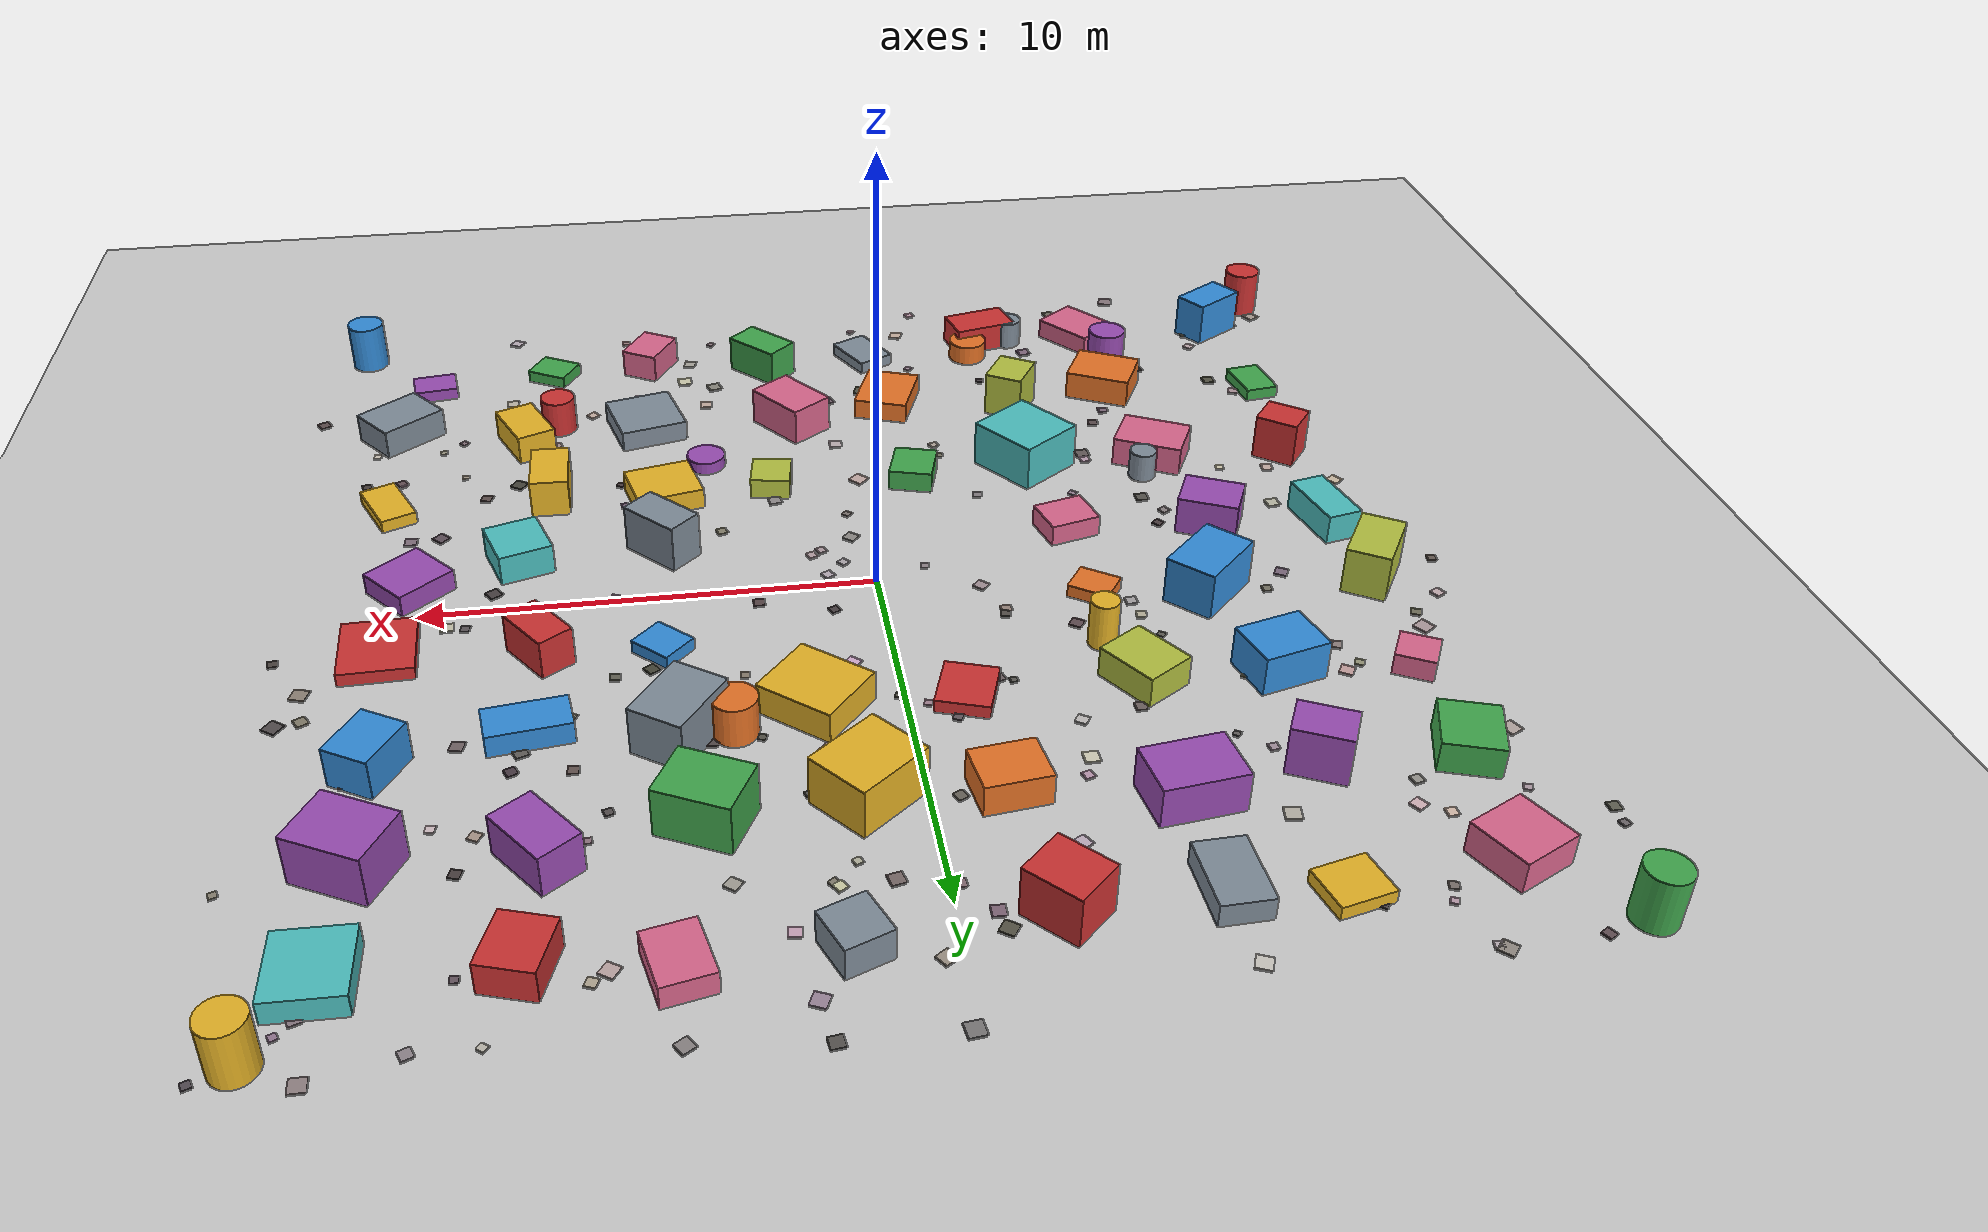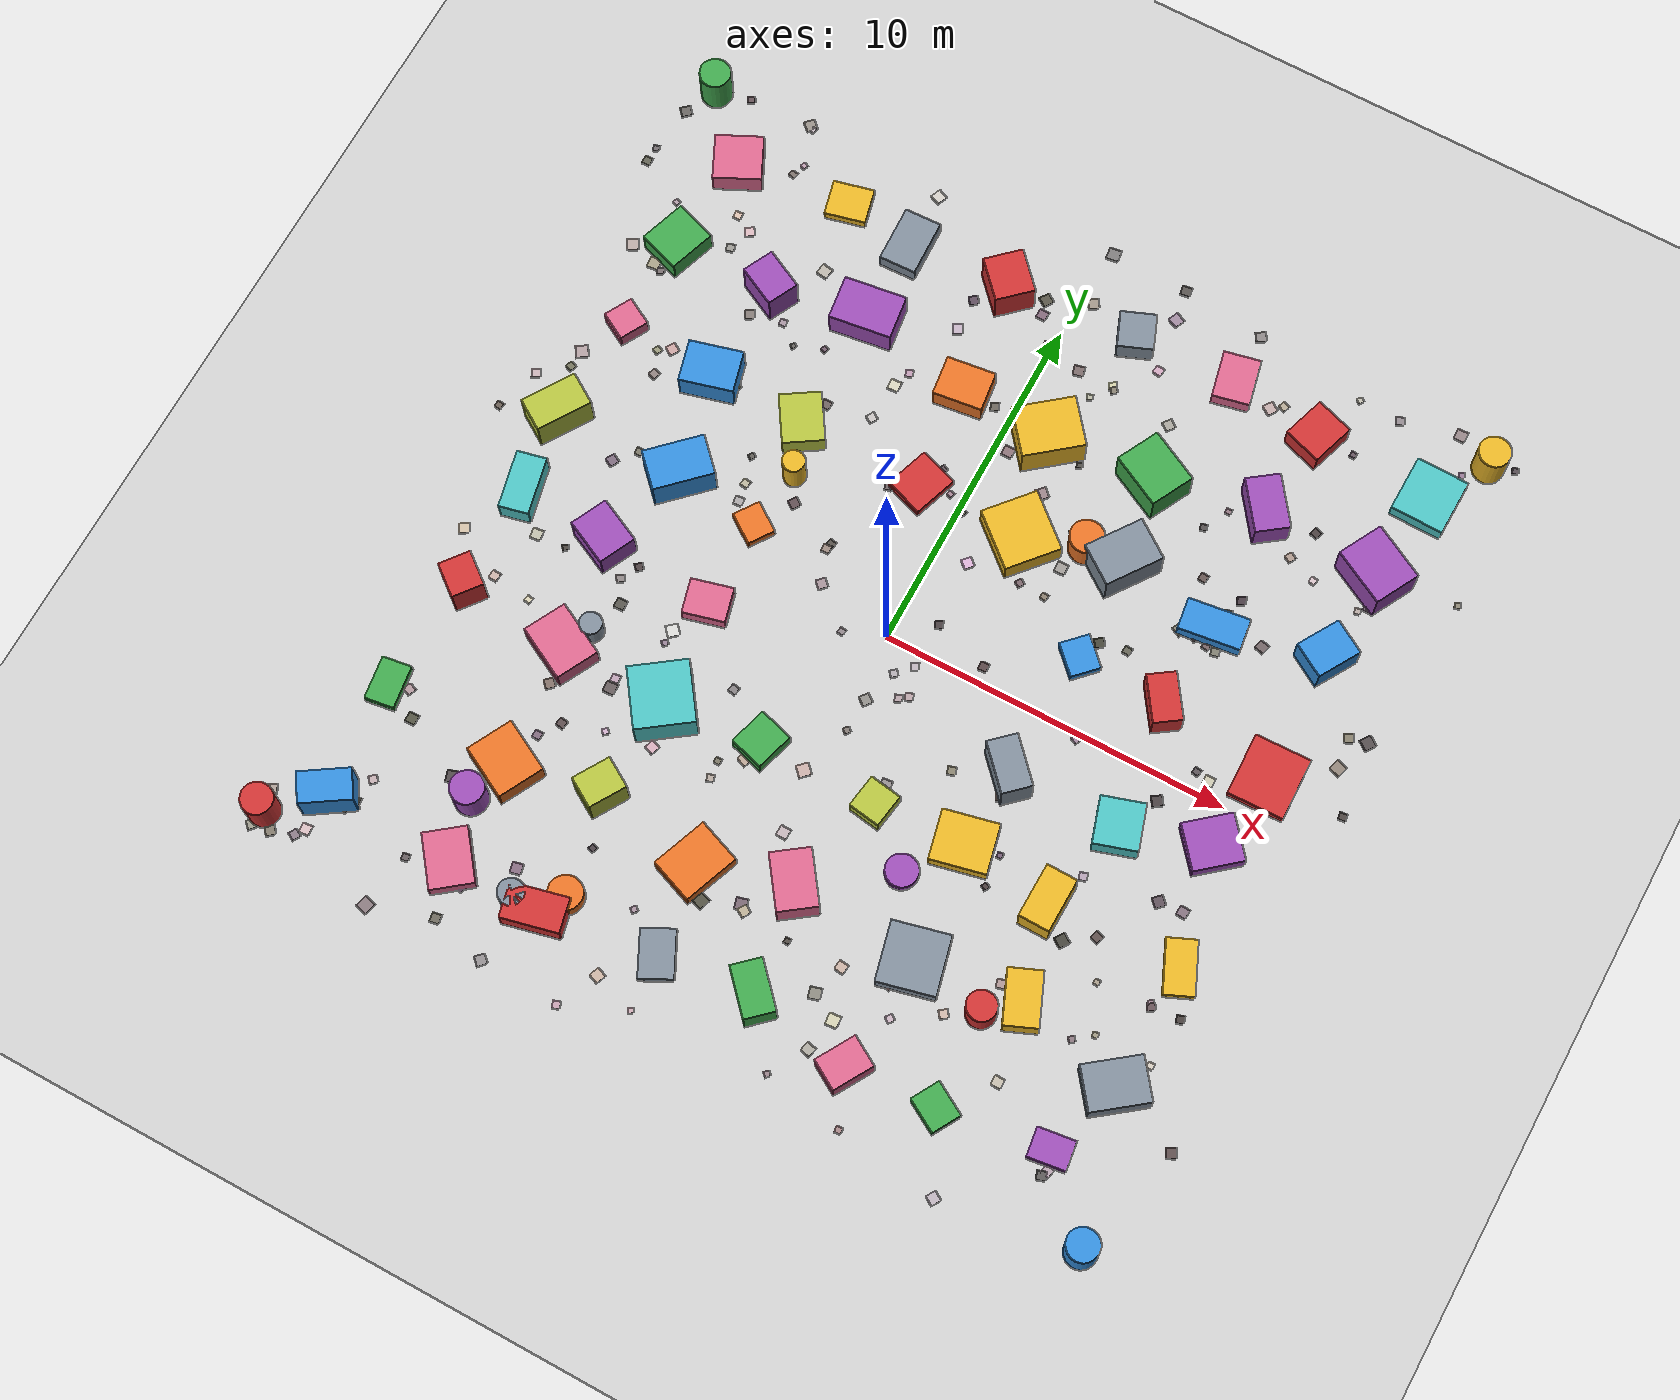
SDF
<?xml version="1.0" ?>
<sdf version="1.6">
  <world name="town_world">

    <physics name="default_physics" default="0" type="ode">
      <gravity>0 0 -9.8066</gravity>
      <max_step_size>0.004</max_step_size>
      <real_time_factor>1.0</real_time_factor>
      <real_time_update_rate>250</real_time_update_rate>
    </physics>

    <plugin name="gazebo_ros_state" filename="libgazebo_ros_state.so">
      <ros><namespace>/gazebo</namespace></ros>
      <update_rate>50.0</update_rate>
    </plugin>

    <scene>
      <ambient>0.6 0.6 0.6 1</ambient>
      <background>0.7 0.8 0.9 1</background>
      <shadows>true</shadows>
    </scene>

    <light name="sun" type="directional">
      <cast_shadows>true</cast_shadows>
      <pose>0 0 10 0 0 0</pose>
      <diffuse>0.9 0.9 0.9 1</diffuse>
      <specular>0.2 0.2 0.2 1</specular>
      <direction>-0.4 0.3 -0.9</direction>
    </light>

    <!-- textured ground: non-repetitive features for the downward camera -->
    <model name="ground_plane">
      <static>true</static>
      <link name="link">
        <collision name="collision">
          <geometry><plane><normal>0 0 1</normal><size>60 60</size></plane></geometry>
          <surface><friction><ode><mu>1.0</mu><mu2>1.0</mu2></ode></friction></surface>
        </collision>
        <visual name="visual">
          <cast_shadows>false</cast_shadows>
          <geometry><plane><normal>0 0 1</normal><size>60 60</size></plane></geometry>
          <material><script>
            <uri>file://media/materials/scripts/gazebo.material</uri>
            <name>Gazebo/CheckerBoard</name>
          </script></material>
        </visual>
      </link>
    </model>
    <model name="bld_0"><static>true</static><pose>-10.68 -10.85 0.55 0 0 0.574</pose><link name="l">
      <collision name="c"><geometry><box><size>1.45 0.87 1.10</size></box></geometry></collision>
      <visual name="v"><geometry><box><size>1.45 0.87 1.10</size></box></geometry>
        <material><ambient>0.2 0.55 0.85 1</ambient><diffuse>0.2 0.55 0.85 1</diffuse></material></visual>
    </link></model>
    <model name="bld_1"><static>true</static><pose>-10.94 -7.49 0.15 0 0 0.142</pose><link name="l">
      <collision name="c"><geometry><box><size>0.84 1.23 0.30</size></box></geometry></collision>
      <visual name="v"><geometry><box><size>0.84 1.23 0.30</size></box></geometry>
        <material><ambient>0.25 0.65 0.3 1</ambient><diffuse>0.25 0.65 0.3 1</diffuse></material></visual>
    </link></model>
    <model name="bld_2"><static>true</static><pose>-10.58 -4.17 0.55 0 0 0.906</pose><link name="l">
      <collision name="c"><geometry><box><size>0.92 1.02 1.10</size></box></geometry></collision>
      <visual name="v"><geometry><box><size>0.92 1.02 1.10</size></box></geometry>
        <material><ambient>0.8 0.2 0.2 1</ambient><diffuse>0.8 0.2 0.2 1</diffuse></material></visual>
    </link></model>
    <model name="bld_3"><static>true</static><pose>-10.60 -1.02 0.35 0 0 0.226</pose><link name="l">
      <collision name="c"><geometry><box><size>0.85 1.66 0.70</size></box></geometry></collision>
      <visual name="v"><geometry><box><size>0.85 1.66 0.70</size></box></geometry>
        <material><ambient>0.3 0.75 0.75 1</ambient><diffuse>0.3 0.75 0.75 1</diffuse></material></visual>
    </link></model>
    <model name="bld_4"><static>true</static><pose>-10.88 1.31 0.55 0 0 1.003</pose><link name="l">
      <collision name="c"><geometry><box><size>1.62 0.98 1.10</size></box></geometry></collision>
      <visual name="v"><geometry><box><size>1.62 0.98 1.10</size></box></geometry>
        <material><ambient>0.7 0.75 0.25 1</ambient><diffuse>0.7 0.75 0.25 1</diffuse></material></visual>
    </link></model>
    <model name="bld_5"><static>true</static><pose>-10.63 4.55 0.25 0 0 1.068</pose><link name="l">
      <collision name="c"><geometry><box><size>0.86 0.86 0.50</size></box></geometry></collision>
      <visual name="v"><geometry><box><size>0.86 0.86 0.50</size></box></geometry>
        <material><ambient>0.85 0.4 0.55 1</ambient><diffuse>0.85 0.4 0.55 1</diffuse></material></visual>
    </link></model>
    <model name="bld_6"><static>true</static><pose>-10.57 7.31 0.35 0 0 1.247</pose><link name="l">
      <collision name="c"><geometry><box><size>1.39 1.25 0.70</size></box></geometry></collision>
      <visual name="v"><geometry><box><size>1.39 1.25 0.70</size></box></geometry>
        <material><ambient>0.25 0.65 0.3 1</ambient><diffuse>0.25 0.65 0.3 1</diffuse></material></visual>
    </link></model>
    <model name="bld_7"><static>true</static><pose>-10.30 10.24 0.35 0 0 0.452</pose><link name="l">
      <collision name="c"><geometry><box><size>1.37 1.33 0.70</size></box></geometry></collision>
      <visual name="v"><geometry><box><size>1.37 1.33 0.70</size></box></geometry>
        <material><ambient>0.85 0.4 0.55 1</ambient><diffuse>0.85 0.4 0.55 1</diffuse></material></visual>
    </link></model>
    <model name="bld_8"><static>true</static><pose>-7.02 -10.88 0.25 0 0 0.662</pose><link name="l">
      <collision name="c"><geometry><box><size>1.22 1.56 0.50</size></box></geometry></collision>
      <visual name="v"><geometry><box><size>1.22 1.56 0.50</size></box></geometry>
        <material><ambient>0.85 0.4 0.55 1</ambient><diffuse>0.85 0.4 0.55 1</diffuse></material></visual>
    </link></model>
    <model name="bld_9"><static>true</static><pose>-7.04 -7.92 0.35 0 0 1.092</pose><link name="l">
      <collision name="c"><geometry><box><size>1.36 1.59 0.70</size></box></geometry></collision>
      <visual name="v"><geometry><box><size>1.36 1.59 0.70</size></box></geometry>
        <material><ambient>0.9 0.45 0.15 1</ambient><diffuse>0.9 0.45 0.15 1</diffuse></material></visual>
    </link></model>
    <model name="bld_10"><static>true</static><pose>-7.41 -4.42 0.35 0 0 1.094</pose><link name="l">
      <collision name="c"><geometry><box><size>1.26 1.64 0.70</size></box></geometry></collision>
      <visual name="v"><geometry><box><size>1.26 1.64 0.70</size></box></geometry>
        <material><ambient>0.85 0.4 0.55 1</ambient><diffuse>0.85 0.4 0.55 1</diffuse></material></visual>
    </link></model>
    <model name="bld_11"><static>true</static><pose>-7.94 -1.27 0.45 0 0 1.125</pose><link name="l">
      <collision name="c"><geometry><box><size>1.11 1.38 0.90</size></box></geometry></collision>
      <visual name="v"><geometry><box><size>1.11 1.38 0.90</size></box></geometry>
        <material><ambient>0.6 0.3 0.7 1</ambient><diffuse>0.6 0.3 0.7 1</diffuse></material></visual>
    </link></model>
    <model name="bld_12"><static>true</static><pose>-7.11 1.35 0.55 0 0 0.775</pose><link name="l">
      <collision name="c"><geometry><box><size>1.74 1.16 1.10</size></box></geometry></collision>
      <visual name="v"><geometry><box><size>1.74 1.16 1.10</size></box></geometry>
        <material><ambient>0.2 0.55 0.85 1</ambient><diffuse>0.2 0.55 0.85 1</diffuse></material></visual>
    </link></model>
    <model name="bld_13"><static>true</static><pose>-7.78 4.29 0.45 0 0 0.261</pose><link name="l">
      <collision name="c"><geometry><box><size>1.54 1.20 0.90</size></box></geometry></collision>
      <visual name="v"><geometry><box><size>1.54 1.20 0.90</size></box></geometry>
        <material><ambient>0.2 0.55 0.85 1</ambient><diffuse>0.2 0.55 0.85 1</diffuse></material></visual>
    </link></model>
    <model name="bld_14"><static>true</static><pose>-7.60 7.28 0.55 0 0 1.109</pose><link name="l">
      <collision name="c"><geometry><box><size>0.94 1.23 1.10</size></box></geometry></collision>
      <visual name="v"><geometry><box><size>0.94 1.23 1.10</size></box></geometry>
        <material><ambient>0.6 0.3 0.7 1</ambient><diffuse>0.6 0.3 0.7 1</diffuse></material></visual>
    </link></model>
    <model name="bld_15"><static>true</static><pose>-7.01 10.68 0.15 0 0 0.238</pose><link name="l">
      <collision name="c"><geometry><box><size>1.18 1.03 0.30</size></box></geometry></collision>
      <visual name="v"><geometry><box><size>1.18 1.03 0.30</size></box></geometry>
        <material><ambient>0.9 0.7 0.15 1</ambient><diffuse>0.9 0.7 0.15 1</diffuse></material></visual>
    </link></model>
    <model name="bld_16"><static>true</static><pose>-4.34 -10.99 0.35 0 0 0.229</pose><link name="l">
      <collision name="c"><geometry><box><size>1.63 0.98 0.70</size></box></geometry></collision>
      <visual name="v"><geometry><box><size>1.63 0.98 0.70</size></box></geometry>
        <material><ambient>0.8 0.2 0.2 1</ambient><diffuse>0.8 0.2 0.2 1</diffuse></material></visual>
    </link></model>
    <model name="bld_17"><static>true</static><pose>-4.47 -7.39 0.55 0 0 1.028</pose><link name="l">
      <collision name="c"><geometry><box><size>1.12 0.93 1.10</size></box></geometry></collision>
      <visual name="v"><geometry><box><size>1.12 0.93 1.10</size></box></geometry>
        <material><ambient>0.7 0.75 0.25 1</ambient><diffuse>0.7 0.75 0.25 1</diffuse></material></visual>
    </link></model>
    <model name="bld_18"><static>true</static><pose>-4.26 -4.54 0.55 0 0 0.625</pose><link name="l">
      <collision name="c"><geometry><box><size>1.67 1.75 1.10</size></box></geometry></collision>
      <visual name="v"><geometry><box><size>1.67 1.75 1.10</size></box></geometry>
        <material><ambient>0.3 0.75 0.75 1</ambient><diffuse>0.3 0.75 0.75 1</diffuse></material></visual>
    </link></model>
    <model name="bld_19"><static>true</static><pose>-4.61 -1.52 0.25 0 0 0.255</pose><link name="l">
      <collision name="c"><geometry><box><size>1.20 0.99 0.50</size></box></geometry></collision>
      <visual name="v"><geometry><box><size>1.20 0.99 0.50</size></box></geometry>
        <material><ambient>0.85 0.4 0.55 1</ambient><diffuse>0.85 0.4 0.55 1</diffuse></material></visual>
    </link></model>
    <model name="bld_20"><static>true</static><pose>-4.66 1.05 0.15 0 0 0.964</pose><link name="l">
      <collision name="c"><geometry><box><size>0.80 0.95 0.30</size></box></geometry></collision>
      <visual name="v"><geometry><box><size>0.80 0.95 0.30</size></box></geometry>
        <material><ambient>0.9 0.45 0.15 1</ambient><diffuse>0.9 0.45 0.15 1</diffuse></material></visual>
    </link></model>
    <model name="bld_21"><static>true</static><pose>-4.93 4.21 0.35 0 0 0.572</pose><link name="l">
      <collision name="c"><geometry><box><size>1.18 1.43 0.70</size></box></geometry></collision>
      <visual name="v"><geometry><box><size>1.18 1.43 0.70</size></box></geometry>
        <material><ambient>0.7 0.75 0.25 1</ambient><diffuse>0.7 0.75 0.25 1</diffuse></material></visual>
    </link></model>
    <model name="bld_22"><static>true</static><pose>-4.88 7.85 0.45 0 0 0.135</pose><link name="l">
      <collision name="c"><geometry><box><size>1.79 1.27 0.90</size></box></geometry></collision>
      <visual name="v"><geometry><box><size>1.79 1.27 0.90</size></box></geometry>
        <material><ambient>0.6 0.3 0.7 1</ambient><diffuse>0.6 0.3 0.7 1</diffuse></material></visual>
    </link></model>
    <model name="bld_23"><static>true</static><pose>-4.90 10.34 0.25 0 0 0.036</pose><link name="l">
      <collision name="c"><geometry><box><size>1.06 1.63 0.50</size></box></geometry></collision>
      <visual name="v"><geometry><box><size>1.06 1.63 0.50</size></box></geometry>
        <material><ambient>0.5 0.55 0.6 1</ambient><diffuse>0.5 0.55 0.6 1</diffuse></material></visual>
    </link></model>
    <model name="bld_24"><static>true</static><pose>-1.05 -10.47 0.15 0 0 0.468</pose><link name="l">
      <collision name="c"><geometry><box><size>0.95 1.34 0.30</size></box></geometry></collision>
      <visual name="v"><geometry><box><size>0.95 1.34 0.30</size></box></geometry>
        <material><ambient>0.5 0.55 0.6 1</ambient><diffuse>0.5 0.55 0.6 1</diffuse></material></visual>
    </link></model>
    <model name="bld_25"><static>true</static><pose>-1.36 -7.91 0.25 0 0 1.212</pose><link name="l">
      <collision name="c"><geometry><box><size>1.65 1.32 0.50</size></box></geometry></collision>
      <visual name="v"><geometry><box><size>1.65 1.32 0.50</size></box></geometry>
        <material><ambient>0.9 0.45 0.15 1</ambient><diffuse>0.9 0.45 0.15 1</diffuse></material></visual>
    </link></model>
    <model name="bld_26"><static>true</static><pose>-1.47 -4.22 0.25 0 0 1.285</pose><link name="l">
      <collision name="c"><geometry><box><size>1.13 1.02 0.50</size></box></geometry></collision>
      <visual name="v"><geometry><box><size>1.13 1.02 0.50</size></box></geometry>
        <material><ambient>0.25 0.65 0.3 1</ambient><diffuse>0.25 0.65 0.3 1</diffuse></material></visual>
    </link></model>
    <model name="bld_27"><static>true</static><pose>-1.26 4.23 0.15 0 0 1.240</pose><link name="l">
      <collision name="c"><geometry><box><size>1.32 1.16 0.30</size></box></geometry></collision>
      <visual name="v"><geometry><box><size>1.32 1.16 0.30</size></box></geometry>
        <material><ambient>0.8 0.2 0.2 1</ambient><diffuse>0.8 0.2 0.2 1</diffuse></material></visual>
    </link></model>
    <model name="bld_28"><static>true</static><pose>-1.53 7.19 0.35 0 0 0.126</pose><link name="l">
      <collision name="c"><geometry><box><size>1.41 1.14 0.70</size></box></geometry></collision>
      <visual name="v"><geometry><box><size>1.41 1.14 0.70</size></box></geometry>
        <material><ambient>0.9 0.45 0.15 1</ambient><diffuse>0.9 0.45 0.15 1</diffuse></material></visual>
    </link></model>
    <model name="bld_29"><static>true</static><pose>-1.90 10.47 0.55 0 0 0.753</pose><link name="l">
      <collision name="c"><geometry><box><size>1.14 1.28 1.10</size></box></geometry></collision>
      <visual name="v"><geometry><box><size>1.14 1.28 1.10</size></box></geometry>
        <material><ambient>0.8 0.2 0.2 1</ambient><diffuse>0.8 0.2 0.2 1</diffuse></material></visual>
    </link></model>
    <model name="bld_30"><static>true</static><pose>1.65 -10.20 0.45 0 0 0.751</pose><link name="l">
      <collision name="c"><geometry><box><size>0.88 1.46 0.90</size></box></geometry></collision>
      <visual name="v"><geometry><box><size>0.88 1.46 0.90</size></box></geometry>
        <material><ambient>0.25 0.65 0.3 1</ambient><diffuse>0.25 0.65 0.3 1</diffuse></material></visual>
    </link></model>
    <model name="bld_31"><static>true</static><pose>1.18 -7.21 0.45 0 0 0.630</pose><link name="l">
      <collision name="c"><geometry><box><size>1.13 1.60 0.90</size></box></geometry></collision>
      <visual name="v"><geometry><box><size>1.13 1.60 0.90</size></box></geometry>
        <material><ambient>0.85 0.4 0.55 1</ambient><diffuse>0.85 0.4 0.55 1</diffuse></material></visual>
    </link></model>
    <model name="bld_32"><static>true</static><pose>1.95 -4.28 0.25 0 0 1.421</pose><link name="l">
      <collision name="c"><geometry><box><size>0.97 0.93 0.50</size></box></geometry></collision>
      <visual name="v"><geometry><box><size>0.97 0.93 0.50</size></box></geometry>
        <material><ambient>0.7 0.75 0.25 1</ambient><diffuse>0.7 0.75 0.25 1</diffuse></material></visual>
    </link></model>
    <model name="bld_33"><static>true</static><pose>1.81 4.15 0.35 0 0 0.861</pose><link name="l">
      <collision name="c"><geometry><box><size>1.63 1.78 0.70</size></box></geometry></collision>
      <visual name="v"><geometry><box><size>1.63 1.78 0.70</size></box></geometry>
        <material><ambient>0.9 0.7 0.15 1</ambient><diffuse>0.9 0.7 0.15 1</diffuse></material></visual>
    </link></model>
    <model name="bld_34"><static>true</static><pose>1.13 7.01 0.55 0 0 0.681</pose><link name="l">
      <collision name="c"><geometry><box><size>1.77 1.45 1.10</size></box></geometry></collision>
      <visual name="v"><geometry><box><size>1.77 1.45 1.10</size></box></geometry>
        <material><ambient>0.9 0.7 0.15 1</ambient><diffuse>0.9 0.7 0.15 1</diffuse></material></visual>
    </link></model>
    <model name="bld_35"><static>true</static><pose>1.87 10.83 0.35 0 0 0.378</pose><link name="l">
      <collision name="c"><geometry><box><size>1.01 1.05 0.70</size></box></geometry></collision>
      <visual name="v"><geometry><box><size>1.01 1.05 0.70</size></box></geometry>
        <material><ambient>0.5 0.55 0.6 1</ambient><diffuse>0.5 0.55 0.6 1</diffuse></material></visual>
    </link></model>
    <model name="bld_36"><static>true</static><pose>4.59 -10.74 0.35 0 0 1.040</pose><link name="l">
      <collision name="c"><geometry><box><size>1.22 0.93 0.70</size></box></geometry></collision>
      <visual name="v"><geometry><box><size>1.22 0.93 0.70</size></box></geometry>
        <material><ambient>0.85 0.4 0.55 1</ambient><diffuse>0.85 0.4 0.55 1</diffuse></material></visual>
    </link></model>
    <model name="bld_37"><static>true</static><pose>4.82 -7.48 0.25 0 0 0.238</pose><link name="l">
      <collision name="c"><geometry><box><size>1.63 1.68 0.50</size></box></geometry></collision>
      <visual name="v"><geometry><box><size>1.63 1.68 0.50</size></box></geometry>
        <material><ambient>0.5 0.55 0.6 1</ambient><diffuse>0.5 0.55 0.6 1</diffuse></material></visual>
    </link></model>
    <model name="bld_38"><static>true</static><pose>4.51 -4.13 0.25 0 0 0.222</pose><link name="l">
      <collision name="c"><geometry><box><size>1.58 1.41 0.50</size></box></geometry></collision>
      <visual name="v"><geometry><box><size>1.58 1.41 0.50</size></box></geometry>
        <material><ambient>0.9 0.7 0.15 1</ambient><diffuse>0.9 0.7 0.15 1</diffuse></material></visual>
    </link></model>
    <model name="bld_39"><static>true</static><pose>4.62 -1.88 0.55 0 0 0.758</pose><link name="l">
      <collision name="c"><geometry><box><size>0.86 1.48 1.10</size></box></geometry></collision>
      <visual name="v"><geometry><box><size>0.86 1.48 1.10</size></box></geometry>
        <material><ambient>0.5 0.55 0.6 1</ambient><diffuse>0.5 0.55 0.6 1</diffuse></material></visual>
    </link></model>
    <model name="bld_40"><static>true</static><pose>4.78 1.88 0.15 0 0 0.797</pose><link name="l">
      <collision name="c"><geometry><box><size>0.86 0.99 0.30</size></box></geometry></collision>
      <visual name="v"><geometry><box><size>0.86 0.99 0.30</size></box></geometry>
        <material><ambient>0.2 0.55 0.85 1</ambient><diffuse>0.2 0.55 0.85 1</diffuse></material></visual>
    </link></model>
    <model name="bld_41"><static>true</static><pose>4.56 4.76 0.55 0 0 0.952</pose><link name="l">
      <collision name="c"><geometry><box><size>1.71 1.24 1.10</size></box></geometry></collision>
      <visual name="v"><geometry><box><size>1.71 1.24 1.10</size></box></geometry>
        <material><ambient>0.5 0.55 0.6 1</ambient><diffuse>0.5 0.55 0.6 1</diffuse></material></visual>
    </link></model>
    <model name="bld_42"><static>true</static><pose>4.20 7.28 0.55 0 0 1.098</pose><link name="l">
      <collision name="c"><geometry><box><size>1.31 1.61 1.10</size></box></geometry></collision>
      <visual name="v"><geometry><box><size>1.31 1.61 1.10</size></box></geometry>
        <material><ambient>0.25 0.65 0.3 1</ambient><diffuse>0.25 0.65 0.3 1</diffuse></material></visual>
    </link></model>
    <model name="bld_43"><static>true</static><pose>4.88 10.94 0.25 0 0 0.215</pose><link name="l">
      <collision name="c"><geometry><box><size>1.06 1.36 0.50</size></box></geometry></collision>
      <visual name="v"><geometry><box><size>1.06 1.36 0.50</size></box></geometry>
        <material><ambient>0.85 0.4 0.55 1</ambient><diffuse>0.85 0.4 0.55 1</diffuse></material></visual>
    </link></model>
    <model name="bld_44"><static>true</static><pose>7.12 -10.56 0.15 0 0 1.051</pose><link name="l">
      <collision name="c"><geometry><box><size>0.87 1.04 0.30</size></box></geometry></collision>
      <visual name="v"><geometry><box><size>0.87 1.04 0.30</size></box></geometry>
        <material><ambient>0.25 0.65 0.3 1</ambient><diffuse>0.25 0.65 0.3 1</diffuse></material></visual>
    </link></model>
    <model name="bld_45"><static>true</static><pose>7.78 -7.10 0.35 0 0 0.397</pose><link name="l">
      <collision name="c"><geometry><box><size>0.95 1.52 0.70</size></box></geometry></collision>
      <visual name="v"><geometry><box><size>0.95 1.52 0.70</size></box></geometry>
        <material><ambient>0.9 0.7 0.15 1</ambient><diffuse>0.9 0.7 0.15 1</diffuse></material></visual>
    </link></model>
    <model name="bld_46"><static>true</static><pose>7.14 -4.53 0.45 0 0 1.554</pose><link name="l">
      <collision name="c"><geometry><box><size>1.55 0.89 0.90</size></box></geometry></collision>
      <visual name="v"><geometry><box><size>1.55 0.89 0.90</size></box></geometry>
        <material><ambient>0.9 0.7 0.15 1</ambient><diffuse>0.9 0.7 0.15 1</diffuse></material></visual>
    </link></model>
    <model name="bld_47"><static>true</static><pose>7.83 -1.84 0.35 0 0 0.307</pose><link name="l">
      <collision name="c"><geometry><box><size>1.23 1.32 0.70</size></box></geometry></collision>
      <visual name="v"><geometry><box><size>1.23 1.32 0.70</size></box></geometry>
        <material><ambient>0.3 0.75 0.75 1</ambient><diffuse>0.3 0.75 0.75 1</diffuse></material></visual>
    </link></model>
    <model name="bld_48"><static>true</static><pose>7.32 1.72 0.45 0 0 0.603</pose><link name="l">
      <collision name="c"><geometry><box><size>0.82 1.35 0.90</size></box></geometry></collision>
      <visual name="v"><geometry><box><size>0.82 1.35 0.90</size></box></geometry>
        <material><ambient>0.8 0.2 0.2 1</ambient><diffuse>0.8 0.2 0.2 1</diffuse></material></visual>
    </link></model>
    <model name="bld_49"><static>true</static><pose>7.52 4.30 0.25 0 0 0.132</pose><link name="l">
      <collision name="c"><geometry><box><size>1.76 0.91 0.50</size></box></geometry></collision>
      <visual name="v"><geometry><box><size>1.76 0.91 0.50</size></box></geometry>
        <material><ambient>0.2 0.55 0.85 1</ambient><diffuse>0.2 0.55 0.85 1</diffuse></material></visual>
    </link></model>
    <model name="bld_50"><static>true</static><pose>7.27 7.91 0.45 0 0 0.637</pose><link name="l">
      <collision name="c"><geometry><box><size>0.98 1.56 0.90</size></box></geometry></collision>
      <visual name="v"><geometry><box><size>0.98 1.56 0.90</size></box></geometry>
        <material><ambient>0.6 0.3 0.7 1</ambient><diffuse>0.6 0.3 0.7 1</diffuse></material></visual>
    </link></model>
    <model name="bld_51"><static>true</static><pose>7.54 10.51 0.35 0 0 1.255</pose><link name="l">
      <collision name="c"><geometry><box><size>1.29 1.13 0.70</size></box></geometry></collision>
      <visual name="v"><geometry><box><size>1.29 1.13 0.70</size></box></geometry>
        <material><ambient>0.8 0.2 0.2 1</ambient><diffuse>0.8 0.2 0.2 1</diffuse></material></visual>
    </link></model>
    <model name="bld_52"><static>true</static><pose>10.18 -10.10 0.15 0 0 0.131</pose><link name="l">
      <collision name="c"><geometry><box><size>1.07 0.82 0.30</size></box></geometry></collision>
      <visual name="v"><geometry><box><size>1.07 0.82 0.30</size></box></geometry>
        <material><ambient>0.6 0.3 0.7 1</ambient><diffuse>0.6 0.3 0.7 1</diffuse></material></visual>
    </link></model>
    <model name="bld_53"><static>true</static><pose>10.86 -7.93 0.35 0 0 0.656</pose><link name="l">
      <collision name="c"><geometry><box><size>1.66 1.25 0.70</size></box></geometry></collision>
      <visual name="v"><geometry><box><size>1.66 1.25 0.70</size></box></geometry>
        <material><ambient>0.5 0.55 0.6 1</ambient><diffuse>0.5 0.55 0.6 1</diffuse></material></visual>
    </link></model>
    <model name="bld_54"><static>true</static><pose>10.92 -4.38 0.15 0 0 0.411</pose><link name="l">
      <collision name="c"><geometry><box><size>0.84 1.51 0.30</size></box></geometry></collision>
      <visual name="v"><geometry><box><size>0.84 1.51 0.30</size></box></geometry>
        <material><ambient>0.9 0.7 0.15 1</ambient><diffuse>0.9 0.7 0.15 1</diffuse></material></visual>
    </link></model>
    <model name="bld_55"><static>true</static><pose>10.18 -1.07 0.25 0 0 0.700</pose><link name="l">
      <collision name="c"><geometry><box><size>1.43 1.33 0.50</size></box></geometry></collision>
      <visual name="v"><geometry><box><size>1.43 1.33 0.50</size></box></geometry>
        <material><ambient>0.6 0.3 0.7 1</ambient><diffuse>0.6 0.3 0.7 1</diffuse></material></visual>
    </link></model>
    <model name="bld_56"><static>true</static><pose>10.67 1.27 0.15 0 0 0.029</pose><link name="l">
      <collision name="c"><geometry><box><size>1.60 1.79 0.30</size></box></geometry></collision>
      <visual name="v"><geometry><box><size>1.60 1.79 0.30</size></box></geometry>
        <material><ambient>0.8 0.2 0.2 1</ambient><diffuse>0.8 0.2 0.2 1</diffuse></material></visual>
    </link></model>
    <model name="bld_57"><static>true</static><pose>10.51 4.98 0.45 0 0 1.034</pose><link name="l">
      <collision name="c"><geometry><box><size>1.31 1.05 0.90</size></box></geometry></collision>
      <visual name="v"><geometry><box><size>1.31 1.05 0.90</size></box></geometry>
        <material><ambient>0.2 0.55 0.85 1</ambient><diffuse>0.2 0.55 0.85 1</diffuse></material></visual>
    </link></model>
    <model name="bld_58"><static>true</static><pose>10.65 7.66 0.55 0 0 1.080</pose><link name="l">
      <collision name="c"><geometry><box><size>1.35 1.69 1.10</size></box></geometry></collision>
      <visual name="v"><geometry><box><size>1.35 1.69 1.10</size></box></geometry>
        <material><ambient>0.6 0.3 0.7 1</ambient><diffuse>0.6 0.3 0.7 1</diffuse></material></visual>
    </link></model>
    <model name="bld_59"><static>true</static><pose>10.98 10.34 0.25 0 0 1.553</pose><link name="l">
      <collision name="c"><geometry><box><size>1.63 1.51 0.50</size></box></geometry></collision>
      <visual name="v"><geometry><box><size>1.63 1.51 0.50</size></box></geometry>
        <material><ambient>0.3 0.75 0.75 1</ambient><diffuse>0.3 0.75 0.75 1</diffuse></material></visual>
    </link></model>
    <model name="landmark_0"><static>true</static><pose>-12.00 -12.00 0.60 0 0 0</pose><link name="l">
      <collision name="c"><geometry><cylinder><radius>0.45</radius><length>1.20</length></cylinder></geometry></collision>
      <visual name="v"><geometry><cylinder><radius>0.45</radius><length>1.20</length></cylinder></geometry>
        <material><ambient>0.8 0.2 0.2 1</ambient><diffuse>0.8 0.2 0.2 1</diffuse></material></visual>
    </link></model>
    <model name="landmark_1"><static>true</static><pose>12.00 -12.00 0.60 0 0 0</pose><link name="l">
      <collision name="c"><geometry><cylinder><radius>0.45</radius><length>1.20</length></cylinder></geometry></collision>
      <visual name="v"><geometry><cylinder><radius>0.45</radius><length>1.20</length></cylinder></geometry>
        <material><ambient>0.2 0.55 0.85 1</ambient><diffuse>0.2 0.55 0.85 1</diffuse></material></visual>
    </link></model>
    <model name="landmark_2"><static>true</static><pose>12.00 12.00 0.60 0 0 0</pose><link name="l">
      <collision name="c"><geometry><cylinder><radius>0.45</radius><length>1.20</length></cylinder></geometry></collision>
      <visual name="v"><geometry><cylinder><radius>0.45</radius><length>1.20</length></cylinder></geometry>
        <material><ambient>0.9 0.7 0.15 1</ambient><diffuse>0.9 0.7 0.15 1</diffuse></material></visual>
    </link></model>
    <model name="landmark_3"><static>true</static><pose>-12.00 12.00 0.60 0 0 0</pose><link name="l">
      <collision name="c"><geometry><cylinder><radius>0.45</radius><length>1.20</length></cylinder></geometry></collision>
      <visual name="v"><geometry><cylinder><radius>0.45</radius><length>1.20</length></cylinder></geometry>
        <material><ambient>0.25 0.65 0.3 1</ambient><diffuse>0.25 0.65 0.3 1</diffuse></material></visual>
    </link></model>
    <model name="tank_0"><static>true</static><pose>10.60 7.41 0.35 0 0 0</pose><link name="l">
      <collision name="c"><geometry><cylinder><radius>0.30</radius><length>0.70</length></cylinder></geometry></collision>
      <visual name="v"><geometry><cylinder><radius>0.30</radius><length>0.70</length></cylinder></geometry>
        <material><ambient>0.3 0.75 0.75 1</ambient><diffuse>0.3 0.75 0.75 1</diffuse></material></visual>
    </link></model>
    <model name="tank_1"><static>true</static><pose>-7.41 -9.14 0.55 0 0 0</pose><link name="l">
      <collision name="c"><geometry><cylinder><radius>0.47</radius><length>1.10</length></cylinder></geometry></collision>
      <visual name="v"><geometry><cylinder><radius>0.47</radius><length>1.10</length></cylinder></geometry>
        <material><ambient>0.6 0.3 0.7 1</ambient><diffuse>0.6 0.3 0.7 1</diffuse></material></visual>
    </link></model>
    <model name="tank_2"><static>true</static><pose>2.17 4.24 0.25 0 0 0</pose><link name="l">
      <collision name="c"><geometry><cylinder><radius>0.31</radius><length>0.50</length></cylinder></geometry></collision>
      <visual name="v"><geometry><cylinder><radius>0.31</radius><length>0.50</length></cylinder></geometry>
        <material><ambient>0.9 0.7 0.15 1</ambient><diffuse>0.9 0.7 0.15 1</diffuse></material></visual>
    </link></model>
    <model name="tank_3"><static>true</static><pose>-5.08 -10.92 0.35 0 0 0</pose><link name="l">
      <collision name="c"><geometry><cylinder><radius>0.37</radius><length>0.70</length></cylinder></geometry></collision>
      <visual name="v"><geometry><cylinder><radius>0.37</radius><length>0.70</length></cylinder></geometry>
        <material><ambient>0.5 0.55 0.6 1</ambient><diffuse>0.5 0.55 0.6 1</diffuse></material></visual>
    </link></model>
    <model name="tank_4"><static>true</static><pose>-3.88 -10.24 0.25 0 0 0</pose><link name="l">
      <collision name="c"><geometry><cylinder><radius>0.48</radius><length>0.50</length></cylinder></geometry></collision>
      <visual name="v"><geometry><cylinder><radius>0.48</radius><length>0.50</length></cylinder></geometry>
        <material><ambient>0.9 0.45 0.15 1</ambient><diffuse>0.9 0.45 0.15 1</diffuse></material></visual>
    </link></model>
    <model name="tank_5"><static>true</static><pose>-6.97 -3.62 0.35 0 0 0</pose><link name="l">
      <collision name="c"><geometry><cylinder><radius>0.32</radius><length>0.70</length></cylinder></geometry></collision>
      <visual name="v"><geometry><cylinder><radius>0.32</radius><length>0.70</length></cylinder></geometry>
        <material><ambient>0.5 0.55 0.6 1</ambient><diffuse>0.5 0.55 0.6 1</diffuse></material></visual>
    </link></model>
    <model name="tank_6"><static>true</static><pose>3.43 -5.54 0.15 0 0 0</pose><link name="l">
      <collision name="c"><geometry><cylinder><radius>0.46</radius><length>0.30</length></cylinder></geometry></collision>
      <visual name="v"><geometry><cylinder><radius>0.46</radius><length>0.30</length></cylinder></geometry>
        <material><ambient>0.6 0.3 0.7 1</ambient><diffuse>0.6 0.3 0.7 1</diffuse></material></visual>
    </link></model>
    <model name="tank_7"><static>true</static><pose>6.97 -7.83 0.45 0 0 0</pose><link name="l">
      <collision name="c"><geometry><cylinder><radius>0.42</radius><length>0.90</length></cylinder></geometry></collision>
      <visual name="v"><geometry><cylinder><radius>0.42</radius><length>0.90</length></cylinder></geometry>
        <material><ambient>0.8 0.2 0.2 1</ambient><diffuse>0.8 0.2 0.2 1</diffuse></material></visual>
    </link></model>
    <model name="tank_8"><static>true</static><pose>-4.41 2.85 0.55 0 0 0</pose><link name="l">
      <collision name="c"><geometry><cylinder><radius>0.32</radius><length>1.10</length></cylinder></geometry></collision>
      <visual name="v"><geometry><cylinder><radius>0.32</radius><length>1.10</length></cylinder></geometry>
        <material><ambient>0.9 0.7 0.15 1</ambient><diffuse>0.9 0.7 0.15 1</diffuse></material></visual>
    </link></model>
    <model name="tank_9"><static>true</static><pose>3.47 4.75 0.45 0 0 0</pose><link name="l">
      <collision name="c"><geometry><cylinder><radius>0.48</radius><length>0.90</length></cylinder></geometry></collision>
      <visual name="v"><geometry><cylinder><radius>0.48</radius><length>0.90</length></cylinder></geometry>
        <material><ambient>0.9 0.45 0.15 1</ambient><diffuse>0.9 0.45 0.15 1</diffuse></material></visual>
    </link></model>
    <model name="ft_0"><static>true</static><pose>5.74 -0.15 0.02 0 0 1.123</pose><link name="l">
      <collision name="c"><geometry><box><size>0.21 0.21 0.04</size></box></geometry></collision>
      <visual name="v"><geometry><box><size>0.21 0.21 0.04</size></box></geometry>
        <material><ambient>0.6212243019486343 0.5149641599541805 0.5994637013708025 1</ambient><diffuse>0.6212243019486343 0.5149641599541805 0.5994637013708025 1</diffuse></material></visual>
    </link></model>
    <model name="ft_1"><static>true</static><pose>0.34 -1.84 0.02 0 0 0.893</pose><link name="l">
      <collision name="c"><geometry><box><size>0.29 0.29 0.04</size></box></geometry></collision>
      <visual name="v"><geometry><box><size>0.29 0.29 0.04</size></box></geometry>
        <material><ambient>0.5533246210484546 0.5433523449996879 0.5259756838779945 1</ambient><diffuse>0.5533246210484546 0.5433523449996879 0.5259756838779945 1</diffuse></material></visual>
    </link></model>
    <model name="ft_2"><static>true</static><pose>8.14 -12.58 0.02 0 0 1.009</pose><link name="l">
      <collision name="c"><geometry><box><size>0.29 0.29 0.04</size></box></geometry></collision>
      <visual name="v"><geometry><box><size>0.29 0.29 0.04</size></box></geometry>
        <material><ambient>0.7287803123570817 0.686683942190973 0.722378371948897 1</ambient><diffuse>0.7287803123570817 0.686683942190973 0.722378371948897 1</diffuse></material></visual>
    </link></model>
    <model name="ft_3"><static>true</static><pose>-10.79 -11.91 0.02 0 0 0.080</pose><link name="l">
      <collision name="c"><geometry><box><size>0.28 0.28 0.04</size></box></geometry></collision>
      <visual name="v"><geometry><box><size>0.28 0.28 0.04</size></box></geometry>
        <material><ambient>0.8257096429388961 0.7227631809551837 0.7351104986890425 1</ambient><diffuse>0.8257096429388961 0.7227631809551837 0.7351104986890425 1</diffuse></material></visual>
    </link></model>
    <model name="ft_4"><static>true</static><pose>-12.51 0.82 0.02 0 0 1.464</pose><link name="l">
      <collision name="c"><geometry><box><size>0.20 0.20 0.04</size></box></geometry></collision>
      <visual name="v"><geometry><box><size>0.20 0.20 0.04</size></box></geometry>
        <material><ambient>0.4082757368831976 0.36393278863417755 0.3323455571166107 1</ambient><diffuse>0.4082757368831976 0.36393278863417755 0.3323455571166107 1</diffuse></material></visual>
    </link></model>
    <model name="ft_5"><static>true</static><pose>10.34 -10.61 0.02 0 0 1.328</pose><link name="l">
      <collision name="c"><geometry><box><size>0.26 0.26 0.04</size></box></geometry></collision>
      <visual name="v"><geometry><box><size>0.26 0.26 0.04</size></box></geometry>
        <material><ambient>0.69743674577827 0.6240466522581352 0.6708251790984469 1</ambient><diffuse>0.69743674577827 0.6240466522581352 0.6708251790984469 1</diffuse></material></visual>
    </link></model>
    <model name="ft_6"><static>true</static><pose>-6.90 6.67 0.02 0 0 0.120</pose><link name="l">
      <collision name="c"><geometry><box><size>0.20 0.20 0.04</size></box></geometry></collision>
      <visual name="v"><geometry><box><size>0.20 0.20 0.04</size></box></geometry>
        <material><ambient>0.6399593680012304 0.5708872816822584 0.620188623328072 1</ambient><diffuse>0.6399593680012304 0.5708872816822584 0.620188623328072 1</diffuse></material></visual>
    </link></model>
    <model name="ft_7"><static>true</static><pose>10.67 -5.53 0.02 0 0 0.521</pose><link name="l">
      <collision name="c"><geometry><box><size>0.16 0.16 0.04</size></box></geometry></collision>
      <visual name="v"><geometry><box><size>0.16 0.16 0.04</size></box></geometry>
        <material><ambient>0.6296757056240572 0.528712259388979 0.5792645326275048 1</ambient><diffuse>0.6296757056240572 0.528712259388979 0.5792645326275048 1</diffuse></material></visual>
    </link></model>
    <model name="ft_8"><static>true</static><pose>3.94 5.02 0.02 0 0 1.527</pose><link name="l">
      <collision name="c"><geometry><box><size>0.27 0.27 0.04</size></box></geometry></collision>
      <visual name="v"><geometry><box><size>0.27 0.27 0.04</size></box></geometry>
        <material><ambient>0.3300646052321905 0.2958976836511722 0.2961206323725841 1</ambient><diffuse>0.3300646052321905 0.2958976836511722 0.2961206323725841 1</diffuse></material></visual>
    </link></model>
    <model name="ft_9"><static>true</static><pose>-10.41 -7.34 0.02 0 0 1.204</pose><link name="l">
      <collision name="c"><geometry><box><size>0.25 0.25 0.04</size></box></geometry></collision>
      <visual name="v"><geometry><box><size>0.25 0.25 0.04</size></box></geometry>
        <material><ambient>0.6753225528442965 0.578824841034194 0.6031842747153561 1</ambient><diffuse>0.6753225528442965 0.578824841034194 0.6031842747153561 1</diffuse></material></visual>
    </link></model>
    <model name="ft_10"><static>true</static><pose>12.83 1.28 0.02 0 0 0.120</pose><link name="l">
      <collision name="c"><geometry><box><size>0.21 0.21 0.04</size></box></geometry></collision>
      <visual name="v"><geometry><box><size>0.21 0.21 0.04</size></box></geometry>
        <material><ambient>0.30151255698317736 0.2697298270147592 0.25867298229221747 1</ambient><diffuse>0.30151255698317736 0.2697298270147592 0.25867298229221747 1</diffuse></material></visual>
    </link></model>
    <model name="ft_11"><static>true</static><pose>0.17 12.86 0.02 0 0 0.117</pose><link name="l">
      <collision name="c"><geometry><box><size>0.35 0.35 0.04</size></box></geometry></collision>
      <visual name="v"><geometry><box><size>0.35 0.35 0.04</size></box></geometry>
        <material><ambient>0.48210900817738717 0.47406306957370253 0.4754111695139394 1</ambient><diffuse>0.48210900817738717 0.47406306957370253 0.4754111695139394 1</diffuse></material></visual>
    </link></model>
    <model name="ft_12"><static>true</static><pose>-10.65 6.43 0.02 0 0 0.439</pose><link name="l">
      <collision name="c"><geometry><box><size>0.20 0.20 0.04</size></box></geometry></collision>
      <visual name="v"><geometry><box><size>0.20 0.20 0.04</size></box></geometry>
        <material><ambient>0.46573214590223905 0.428787080923408 0.4314233538779299 1</ambient><diffuse>0.46573214590223905 0.428787080923408 0.4314233538779299 1</diffuse></material></visual>
    </link></model>
    <model name="ft_13"><static>true</static><pose>-10.07 -3.51 0.02 0 0 1.491</pose><link name="l">
      <collision name="c"><geometry><box><size>0.25 0.25 0.04</size></box></geometry></collision>
      <visual name="v"><geometry><box><size>0.25 0.25 0.04</size></box></geometry>
        <material><ambient>0.77568713941935 0.6816863497658909 0.6452266882276717 1</ambient><diffuse>0.77568713941935 0.6816863497658909 0.6452266882276717 1</diffuse></material></visual>
    </link></model>
    <model name="ft_14"><static>true</static><pose>4.72 -2.46 0.02 0 0 0.520</pose><link name="l">
      <collision name="c"><geometry><box><size>0.30 0.30 0.04</size></box></geometry></collision>
      <visual name="v"><geometry><box><size>0.30 0.30 0.04</size></box></geometry>
        <material><ambient>0.49970871661883653 0.43735567713640094 0.4118508649570005 1</ambient><diffuse>0.49970871661883653 0.43735567713640094 0.4118508649570005 1</diffuse></material></visual>
    </link></model>
    <model name="ft_15"><static>true</static><pose>-4.56 -4.20 0.02 0 0 1.162</pose><link name="l">
      <collision name="c"><geometry><box><size>0.23 0.23 0.04</size></box></geometry></collision>
      <visual name="v"><geometry><box><size>0.23 0.23 0.04</size></box></geometry>
        <material><ambient>0.8139286157178828 0.6830067551446627 0.6530510045945481 1</ambient><diffuse>0.8139286157178828 0.6830067551446627 0.6530510045945481 1</diffuse></material></visual>
    </link></model>
    <model name="ft_16"><static>true</static><pose>-6.42 -11.31 0.02 0 0 1.186</pose><link name="l">
      <collision name="c"><geometry><box><size>0.23 0.23 0.04</size></box></geometry></collision>
      <visual name="v"><geometry><box><size>0.23 0.23 0.04</size></box></geometry>
        <material><ambient>0.7719831567518859 0.6293825349514359 0.7604675595468173 1</ambient><diffuse>0.7719831567518859 0.6293825349514359 0.7604675595468173 1</diffuse></material></visual>
    </link></model>
    <model name="ft_17"><static>true</static><pose>9.21 -5.70 0.02 0 0 1.525</pose><link name="l">
      <collision name="c"><geometry><box><size>0.16 0.16 0.04</size></box></geometry></collision>
      <visual name="v"><geometry><box><size>0.16 0.16 0.04</size></box></geometry>
        <material><ambient>0.6471869079125964 0.5999375387873627 0.537024614238678 1</ambient><diffuse>0.6471869079125964 0.5999375387873627 0.537024614238678 1</diffuse></material></visual>
    </link></model>
    <model name="ft_18"><static>true</static><pose>-1.66 -4.79 0.02 0 0 1.196</pose><link name="l">
      <collision name="c"><geometry><box><size>0.30 0.30 0.04</size></box></geometry></collision>
      <visual name="v"><geometry><box><size>0.30 0.30 0.04</size></box></geometry>
        <material><ambient>0.7210856048293348 0.6385570164520308 0.5810524122165364 1</ambient><diffuse>0.7210856048293348 0.6385570164520308 0.5810524122165364 1</diffuse></material></visual>
    </link></model>
    <model name="ft_19"><static>true</static><pose>-2.60 9.77 0.02 0 0 0.645</pose><link name="l">
      <collision name="c"><geometry><box><size>0.26 0.26 0.04</size></box></geometry></collision>
      <visual name="v"><geometry><box><size>0.26 0.26 0.04</size></box></geometry>
        <material><ambient>0.37206148826884883 0.3036451026613469 0.3671104922487789 1</ambient><diffuse>0.37206148826884883 0.3036451026613469 0.3671104922487789 1</diffuse></material></visual>
    </link></model>
    <model name="ft_20"><static>true</static><pose>2.99 -9.40 0.02 0 0 0.268</pose><link name="l">
      <collision name="c"><geometry><box><size>0.32 0.32 0.04</size></box></geometry></collision>
      <visual name="v"><geometry><box><size>0.32 0.32 0.04</size></box></geometry>
        <material><ambient>0.5413450481696884 0.5318071161237796 0.49263570803236634 1</ambient><diffuse>0.5413450481696884 0.5318071161237796 0.49263570803236634 1</diffuse></material></visual>
    </link></model>
    <model name="ft_21"><static>true</static><pose>-2.21 -5.67 0.02 0 0 0.375</pose><link name="l">
      <collision name="c"><geometry><box><size>0.20 0.20 0.04</size></box></geometry></collision>
      <visual name="v"><geometry><box><size>0.20 0.20 0.04</size></box></geometry>
        <material><ambient>0.6932471676601298 0.6451105557544258 0.61091841863146 1</ambient><diffuse>0.6932471676601298 0.6451105557544258 0.61091841863146 1</diffuse></material></visual>
    </link></model>
    <model name="ft_22"><static>true</static><pose>-0.44 4.39 0.02 0 0 1.275</pose><link name="l">
      <collision name="c"><geometry><box><size>0.17 0.17 0.04</size></box></geometry></collision>
      <visual name="v"><geometry><box><size>0.17 0.17 0.04</size></box></geometry>
        <material><ambient>0.6359230197742147 0.5182989579219701 0.5724076381204705 1</ambient><diffuse>0.6359230197742147 0.5182989579219701 0.5724076381204705 1</diffuse></material></visual>
    </link></model>
    <model name="ft_23"><static>true</static><pose>1.31 -1.22 0.02 0 0 0.383</pose><link name="l">
      <collision name="c"><geometry><box><size>0.22 0.22 0.04</size></box></geometry></collision>
      <visual name="v"><geometry><box><size>0.22 0.22 0.04</size></box></geometry>
        <material><ambient>0.7055487146226783 0.6247525246963589 0.6417368143430442 1</ambient><diffuse>0.7055487146226783 0.6247525246963589 0.6417368143430442 1</diffuse></material></visual>
    </link></model>
    <model name="ft_24"><static>true</static><pose>-8.46 1.45 0.02 0 0 0.032</pose><link name="l">
      <collision name="c"><geometry><box><size>0.21 0.21 0.04</size></box></geometry></collision>
      <visual name="v"><geometry><box><size>0.21 0.21 0.04</size></box></geometry>
        <material><ambient>0.4709832009301672 0.4530254069300979 0.3958276431859622 1</ambient><diffuse>0.4709832009301672 0.4530254069300979 0.3958276431859622 1</diffuse></material></visual>
    </link></model>
    <model name="ft_25"><static>true</static><pose>9.64 -3.05 0.02 0 0 0.782</pose><link name="l">
      <collision name="c"><geometry><box><size>0.30 0.30 0.04</size></box></geometry></collision>
      <visual name="v"><geometry><box><size>0.30 0.30 0.04</size></box></geometry>
        <material><ambient>0.3760029615917763 0.3211245658687852 0.35736156220811865 1</ambient><diffuse>0.3760029615917763 0.3211245658687852 0.35736156220811865 1</diffuse></material></visual>
    </link></model>
    <model name="ft_26"><static>true</static><pose>1.93 -3.64 0.02 0 0 0.145</pose><link name="l">
      <collision name="c"><geometry><box><size>0.29 0.29 0.04</size></box></geometry></collision>
      <visual name="v"><geometry><box><size>0.29 0.29 0.04</size></box></geometry>
        <material><ambient>0.5675354181064378 0.5437343327571231 0.5503541093900503 1</ambient><diffuse>0.5675354181064378 0.5437343327571231 0.5503541093900503 1</diffuse></material></visual>
    </link></model>
    <model name="ft_27"><static>true</static><pose>10.32 -3.00 0.02 0 0 1.520</pose><link name="l">
      <collision name="c"><geometry><box><size>0.28 0.28 0.04</size></box></geometry></collision>
      <visual name="v"><geometry><box><size>0.28 0.28 0.04</size></box></geometry>
        <material><ambient>0.5091020120111565 0.4390512059758533 0.4901979308450359 1</ambient><diffuse>0.5091020120111565 0.4390512059758533 0.4901979308450359 1</diffuse></material></visual>
    </link></model>
    <model name="ft_28"><static>true</static><pose>-9.69 -1.94 0.02 0 0 0.115</pose><link name="l">
      <collision name="c"><geometry><box><size>0.30 0.30 0.04</size></box></geometry></collision>
      <visual name="v"><geometry><box><size>0.30 0.30 0.04</size></box></geometry>
        <material><ambient>0.7325495606955957 0.7279024517637563 0.6578037728114212 1</ambient><diffuse>0.7325495606955957 0.7279024517637563 0.6578037728114212 1</diffuse></material></visual>
    </link></model>
    <model name="ft_29"><static>true</static><pose>11.19 11.13 0.02 0 0 0.351</pose><link name="l">
      <collision name="c"><geometry><box><size>0.26 0.26 0.04</size></box></geometry></collision>
      <visual name="v"><geometry><box><size>0.26 0.26 0.04</size></box></geometry>
        <material><ambient>0.530890852088814 0.4723814157890406 0.5078615697820275 1</ambient><diffuse>0.530890852088814 0.4723814157890406 0.5078615697820275 1</diffuse></material></visual>
    </link></model>
    <model name="ft_30"><static>true</static><pose>-9.05 12.27 0.02 0 0 1.405</pose><link name="l">
      <collision name="c"><geometry><box><size>0.17 0.17 0.04</size></box></geometry></collision>
      <visual name="v"><geometry><box><size>0.17 0.17 0.04</size></box></geometry>
        <material><ambient>0.7452372106391278 0.7006725788215511 0.722359697576769 1</ambient><diffuse>0.7452372106391278 0.7006725788215511 0.722359697576769 1</diffuse></material></visual>
    </link></model>
    <model name="ft_31"><static>true</static><pose>-10.79 7.20 0.02 0 0 1.123</pose><link name="l">
      <collision name="c"><geometry><box><size>0.15 0.15 0.04</size></box></geometry></collision>
      <visual name="v"><geometry><box><size>0.15 0.15 0.04</size></box></geometry>
        <material><ambient>0.32539106264372236 0.2973672315962051 0.2627592527350926 1</ambient><diffuse>0.32539106264372236 0.2973672315962051 0.2627592527350926 1</diffuse></material></visual>
    </link></model>
    <model name="ft_32"><static>true</static><pose>12.02 3.29 0.02 0 0 0.472</pose><link name="l">
      <collision name="c"><geometry><box><size>0.26 0.26 0.04</size></box></geometry></collision>
      <visual name="v"><geometry><box><size>0.26 0.26 0.04</size></box></geometry>
        <material><ambient>0.5124583171244647 0.48825430111477097 0.42015891510734477 1</ambient><diffuse>0.5124583171244647 0.48825430111477097 0.42015891510734477 1</diffuse></material></visual>
    </link></model>
    <model name="ft_33"><static>true</static><pose>11.53 -8.02 0.02 0 0 1.564</pose><link name="l">
      <collision name="c"><geometry><box><size>0.20 0.20 0.04</size></box></geometry></collision>
      <visual name="v"><geometry><box><size>0.20 0.20 0.04</size></box></geometry>
        <material><ambient>0.7242923182296495 0.5796007349743735 0.6572918483046541 1</ambient><diffuse>0.7242923182296495 0.5796007349743735 0.6572918483046541 1</diffuse></material></visual>
    </link></model>
    <model name="ft_34"><static>true</static><pose>-5.76 -4.77 0.02 0 0 0.046</pose><link name="l">
      <collision name="c"><geometry><box><size>0.32 0.32 0.04</size></box></geometry></collision>
      <visual name="v"><geometry><box><size>0.32 0.32 0.04</size></box></geometry>
        <material><ambient>0.3954145601777921 0.3579512218125734 0.3595901778080671 1</ambient><diffuse>0.3954145601777921 0.3579512218125734 0.3595901778080671 1</diffuse></material></visual>
    </link></model>
    <model name="ft_35"><static>true</static><pose>-2.29 3.89 0.02 0 0 0.127</pose><link name="l">
      <collision name="c"><geometry><box><size>0.16 0.16 0.04</size></box></geometry></collision>
      <visual name="v"><geometry><box><size>0.16 0.16 0.04</size></box></geometry>
        <material><ambient>0.3664691351278584 0.3580292428510184 0.3406087536675115 1</ambient><diffuse>0.3664691351278584 0.3580292428510184 0.3406087536675115 1</diffuse></material></visual>
    </link></model>
    <model name="ft_36"><static>true</static><pose>-7.08 -1.97 0.02 0 0 0.569</pose><link name="l">
      <collision name="c"><geometry><box><size>0.22 0.22 0.04</size></box></geometry></collision>
      <visual name="v"><geometry><box><size>0.22 0.22 0.04</size></box></geometry>
        <material><ambient>0.5457660706375425 0.5125641499923063 0.5150211294952293 1</ambient><diffuse>0.5457660706375425 0.5125641499923063 0.5150211294952293 1</diffuse></material></visual>
    </link></model>
    <model name="ft_37"><static>true</static><pose>-2.69 -12.82 0.02 0 0 0.315</pose><link name="l">
      <collision name="c"><geometry><box><size>0.21 0.21 0.04</size></box></geometry></collision>
      <visual name="v"><geometry><box><size>0.21 0.21 0.04</size></box></geometry>
        <material><ambient>0.7570898331919836 0.6158823521154363 0.6807290883607733 1</ambient><diffuse>0.7570898331919836 0.6158823521154363 0.6807290883607733 1</diffuse></material></visual>
    </link></model>
    <model name="ft_38"><static>true</static><pose>6.91 -7.96 0.02 0 0 0.979</pose><link name="l">
      <collision name="c"><geometry><box><size>0.24 0.24 0.04</size></box></geometry></collision>
      <visual name="v"><geometry><box><size>0.24 0.24 0.04</size></box></geometry>
        <material><ambient>0.4090131734034601 0.39996039290546226 0.336127685722852 1</ambient><diffuse>0.4090131734034601 0.39996039290546226 0.336127685722852 1</diffuse></material></visual>
    </link></model>
    <model name="ft_39"><static>true</static><pose>2.86 10.31 0.02 0 0 1.447</pose><link name="l">
      <collision name="c"><geometry><box><size>0.25 0.25 0.04</size></box></geometry></collision>
      <visual name="v"><geometry><box><size>0.25 0.25 0.04</size></box></geometry>
        <material><ambient>0.7962375998435657 0.6459743595343689 0.7317108494645137 1</ambient><diffuse>0.7962375998435657 0.6459743595343689 0.7317108494645137 1</diffuse></material></visual>
    </link></model>
    <model name="ft_40"><static>true</static><pose>-11.59 -12.39 0.02 0 0 0.706</pose><link name="l">
      <collision name="c"><geometry><box><size>0.27 0.27 0.04</size></box></geometry></collision>
      <visual name="v"><geometry><box><size>0.27 0.27 0.04</size></box></geometry>
        <material><ambient>0.49923096024322744 0.47026144523144514 0.4177669339591884 1</ambient><diffuse>0.49923096024322744 0.47026144523144514 0.4177669339591884 1</diffuse></material></visual>
    </link></model>
    <model name="ft_41"><static>true</static><pose>5.51 -4.83 0.02 0 0 1.024</pose><link name="l">
      <collision name="c"><geometry><box><size>0.17 0.17 0.04</size></box></geometry></collision>
      <visual name="v"><geometry><box><size>0.17 0.17 0.04</size></box></geometry>
        <material><ambient>0.2976167154234446 0.24795244630057883 0.2494434930817707 1</ambient><diffuse>0.2976167154234446 0.24795244630057883 0.2494434930817707 1</diffuse></material></visual>
    </link></model>
    <model name="ft_42"><static>true</static><pose>0.64 -0.84 0.02 0 0 0.695</pose><link name="l">
      <collision name="c"><geometry><box><size>0.21 0.21 0.04</size></box></geometry></collision>
      <visual name="v"><geometry><box><size>0.21 0.21 0.04</size></box></geometry>
        <material><ambient>0.6852263899681839 0.6631795048904755 0.6831683646435681 1</ambient><diffuse>0.6852263899681839 0.6631795048904755 0.6831683646435681 1</diffuse></material></visual>
    </link></model>
    <model name="ft_43"><static>true</static><pose>-10.17 -10.97 0.02 0 0 1.191</pose><link name="l">
      <collision name="c"><geometry><box><size>0.17 0.17 0.04</size></box></geometry></collision>
      <visual name="v"><geometry><box><size>0.17 0.17 0.04</size></box></geometry>
        <material><ambient>0.5021098954477079 0.4905787065697542 0.4580375924354526 1</ambient><diffuse>0.5021098954477079 0.4905787065697542 0.4580375924354526 1</diffuse></material></visual>
    </link></model>
    <model name="ft_44"><static>true</static><pose>-3.12 6.99 0.02 0 0 0.307</pose><link name="l">
      <collision name="c"><geometry><box><size>0.21 0.21 0.04</size></box></geometry></collision>
      <visual name="v"><geometry><box><size>0.21 0.21 0.04</size></box></geometry>
        <material><ambient>0.7323617477675497 0.5987438500683856 0.6891899730458133 1</ambient><diffuse>0.7323617477675497 0.5987438500683856 0.6891899730458133 1</diffuse></material></visual>
    </link></model>
    <model name="ft_45"><static>true</static><pose>1.08 -1.39 0.02 0 0 0.389</pose><link name="l">
      <collision name="c"><geometry><box><size>0.21 0.21 0.04</size></box></geometry></collision>
      <visual name="v"><geometry><box><size>0.21 0.21 0.04</size></box></geometry>
        <material><ambient>0.6923918823763431 0.6196262509453655 0.6413850515857581 1</ambient><diffuse>0.6923918823763431 0.6196262509453655 0.6413850515857581 1</diffuse></material></visual>
    </link></model>
    <model name="ft_46"><static>true</static><pose>3.26 -2.48 0.02 0 0 0.306</pose><link name="l">
      <collision name="c"><geometry><box><size>0.23 0.23 0.04</size></box></geometry></collision>
      <visual name="v"><geometry><box><size>0.23 0.23 0.04</size></box></geometry>
        <material><ambient>0.5284303682859834 0.5076459421284903 0.42929724311284856 1</ambient><diffuse>0.5284303682859834 0.5076459421284903 0.42929724311284856 1</diffuse></material></visual>
    </link></model>
    <model name="ft_47"><static>true</static><pose>-11.37 2.75 0.02 0 0 1.172</pose><link name="l">
      <collision name="c"><geometry><box><size>0.22 0.22 0.04</size></box></geometry></collision>
      <visual name="v"><geometry><box><size>0.22 0.22 0.04</size></box></geometry>
        <material><ambient>0.4509825481073093 0.4468120801494546 0.3647173041535964 1</ambient><diffuse>0.4509825481073093 0.4468120801494546 0.3647173041535964 1</diffuse></material></visual>
    </link></model>
    <model name="ft_48"><static>true</static><pose>4.93 11.03 0.02 0 0 1.486</pose><link name="l">
      <collision name="c"><geometry><box><size>0.21 0.21 0.04</size></box></geometry></collision>
      <visual name="v"><geometry><box><size>0.21 0.21 0.04</size></box></geometry>
        <material><ambient>0.6829432416959957 0.6277024429303277 0.6563983787654685 1</ambient><diffuse>0.6829432416959957 0.6277024429303277 0.6563983787654685 1</diffuse></material></visual>
    </link></model>
    <model name="ft_49"><static>true</static><pose>-11.30 8.48 0.02 0 0 1.240</pose><link name="l">
      <collision name="c"><geometry><box><size>0.17 0.17 0.04</size></box></geometry></collision>
      <visual name="v"><geometry><box><size>0.17 0.17 0.04</size></box></geometry>
        <material><ambient>0.6793427122687294 0.6067541155414101 0.64895662002616 1</ambient><diffuse>0.6793427122687294 0.6067541155414101 0.64895662002616 1</diffuse></material></visual>
    </link></model>
    <model name="ft_50"><static>true</static><pose>10.75 8.18 0.02 0 0 0.476</pose><link name="l">
      <collision name="c"><geometry><box><size>0.18 0.18 0.04</size></box></geometry></collision>
      <visual name="v"><geometry><box><size>0.18 0.18 0.04</size></box></geometry>
        <material><ambient>0.5479243644309307 0.43929344785069524 0.54036917090025 1</ambient><diffuse>0.5479243644309307 0.43929344785069524 0.54036917090025 1</diffuse></material></visual>
    </link></model>
    <model name="ft_51"><static>true</static><pose>4.99 -9.07 0.02 0 0 0.935</pose><link name="l">
      <collision name="c"><geometry><box><size>0.20 0.20 0.04</size></box></geometry></collision>
      <visual name="v"><geometry><box><size>0.20 0.20 0.04</size></box></geometry>
        <material><ambient>0.7667454227188919 0.684056712904792 0.7335964161770084 1</ambient><diffuse>0.7667454227188919 0.684056712904792 0.7335964161770084 1</diffuse></material></visual>
    </link></model>
    <model name="ft_52"><static>true</static><pose>0.31 -2.82 0.02 0 0 0.855</pose><link name="l">
      <collision name="c"><geometry><box><size>0.18 0.18 0.04</size></box></geometry></collision>
      <visual name="v"><geometry><box><size>0.18 0.18 0.04</size></box></geometry>
        <material><ambient>0.49465406118959043 0.45998336208344476 0.44337722242859967 1</ambient><diffuse>0.49465406118959043 0.45998336208344476 0.44337722242859967 1</diffuse></material></visual>
    </link></model>
    <model name="ft_53"><static>true</static><pose>-8.82 -1.91 0.02 0 0 0.661</pose><link name="l">
      <collision name="c"><geometry><box><size>0.17 0.17 0.04</size></box></geometry></collision>
      <visual name="v"><geometry><box><size>0.17 0.17 0.04</size></box></geometry>
        <material><ambient>0.29329902648132133 0.27127822786717803 0.24686046605223055 1</ambient><diffuse>0.29329902648132133 0.27127822786717803 0.24686046605223055 1</diffuse></material></visual>
    </link></model>
    <model name="ft_54"><static>true</static><pose>12.70 12.28 0.02 0 0 0.369</pose><link name="l">
      <collision name="c"><geometry><box><size>0.18 0.18 0.04</size></box></geometry></collision>
      <visual name="v"><geometry><box><size>0.18 0.18 0.04</size></box></geometry>
        <material><ambient>0.3297586966313748 0.2942056813531969 0.3225872732447674 1</ambient><diffuse>0.3297586966313748 0.2942056813531969 0.3225872732447674 1</diffuse></material></visual>
    </link></model>
    <model name="ft_55"><static>true</static><pose>1.00 7.12 0.02 0 0 0.420</pose><link name="l">
      <collision name="c"><geometry><box><size>0.30 0.30 0.04</size></box></geometry></collision>
      <visual name="v"><geometry><box><size>0.30 0.30 0.04</size></box></geometry>
        <material><ambient>0.7178503550926052 0.6164788899888708 0.6143933183883249 1</ambient><diffuse>0.7178503550926052 0.6164788899888708 0.6143933183883249 1</diffuse></material></visual>
    </link></model>
    <model name="ft_56"><static>true</static><pose>-6.39 -6.23 0.02 0 0 1.425</pose><link name="l">
      <collision name="c"><geometry><box><size>0.24 0.24 0.04</size></box></geometry></collision>
      <visual name="v"><geometry><box><size>0.24 0.24 0.04</size></box></geometry>
        <material><ambient>0.361441851758988 0.30617768249937494 0.30949211069033156 1</ambient><diffuse>0.361441851758988 0.30617768249937494 0.30949211069033156 1</diffuse></material></visual>
    </link></model>
    <model name="ft_57"><static>true</static><pose>-8.11 -11.32 0.02 0 0 0.158</pose><link name="l">
      <collision name="c"><geometry><box><size>0.20 0.20 0.04</size></box></geometry></collision>
      <visual name="v"><geometry><box><size>0.20 0.20 0.04</size></box></geometry>
        <material><ambient>0.3975695364504658 0.35990449406493663 0.36971109602007446 1</ambient><diffuse>0.3975695364504658 0.35990449406493663 0.36971109602007446 1</diffuse></material></visual>
    </link></model>
    <model name="ft_58"><static>true</static><pose>-0.94 -12.04 0.02 0 0 0.587</pose><link name="l">
      <collision name="c"><geometry><box><size>0.15 0.15 0.04</size></box></geometry></collision>
      <visual name="v"><geometry><box><size>0.15 0.15 0.04</size></box></geometry>
        <material><ambient>0.7796950138469161 0.6597956290427879 0.6936630227227756 1</ambient><diffuse>0.7796950138469161 0.6597956290427879 0.6936630227227756 1</diffuse></material></visual>
    </link></model>
    <model name="ft_59"><static>true</static><pose>9.80 -6.94 0.02 0 0 0.118</pose><link name="l">
      <collision name="c"><geometry><box><size>0.16 0.16 0.04</size></box></geometry></collision>
      <visual name="v"><geometry><box><size>0.16 0.16 0.04</size></box></geometry>
        <material><ambient>0.6102959870083563 0.5892926552796498 0.511935999681384 1</ambient><diffuse>0.6102959870083563 0.5892926552796498 0.511935999681384 1</diffuse></material></visual>
    </link></model>
    <model name="ft_60"><static>true</static><pose>0.33 -8.38 0.02 0 0 1.001</pose><link name="l">
      <collision name="c"><geometry><box><size>0.27 0.27 0.04</size></box></geometry></collision>
      <visual name="v"><geometry><box><size>0.27 0.27 0.04</size></box></geometry>
        <material><ambient>0.7149989252289068 0.6670590477058719 0.5729056903240066 1</ambient><diffuse>0.7149989252289068 0.6670590477058719 0.5729056903240066 1</diffuse></material></visual>
    </link></model>
    <model name="ft_61"><static>true</static><pose>5.45 -3.91 0.02 0 0 0.060</pose><link name="l">
      <collision name="c"><geometry><box><size>0.16 0.16 0.04</size></box></geometry></collision>
      <visual name="v"><geometry><box><size>0.16 0.16 0.04</size></box></geometry>
        <material><ambient>0.45400993589178984 0.3672183573323116 0.4539984729818821 1</ambient><diffuse>0.45400993589178984 0.3672183573323116 0.4539984729818821 1</diffuse></material></visual>
    </link></model>
    <model name="ft_62"><static>true</static><pose>6.04 10.76 0.02 0 0 0.975</pose><link name="l">
      <collision name="c"><geometry><box><size>0.31 0.31 0.04</size></box></geometry></collision>
      <visual name="v"><geometry><box><size>0.31 0.31 0.04</size></box></geometry>
        <material><ambient>0.7412998646225746 0.6536774638761262 0.6481643203742109 1</ambient><diffuse>0.7412998646225746 0.6536774638761262 0.6481643203742109 1</diffuse></material></visual>
    </link></model>
    <model name="ft_63"><static>true</static><pose>-10.97 -12.18 0.02 0 0 1.043</pose><link name="l">
      <collision name="c"><geometry><box><size>0.25 0.25 0.04</size></box></geometry></collision>
      <visual name="v"><geometry><box><size>0.25 0.25 0.04</size></box></geometry>
        <material><ambient>0.5401042181101638 0.476174247109453 0.5180511009754373 1</ambient><diffuse>0.5401042181101638 0.476174247109453 0.5180511009754373 1</diffuse></material></visual>
    </link></model>
    <model name="ft_64"><static>true</static><pose>-8.98 0.88 0.02 0 0 1.048</pose><link name="l">
      <collision name="c"><geometry><box><size>0.28 0.28 0.04</size></box></geometry></collision>
      <visual name="v"><geometry><box><size>0.28 0.28 0.04</size></box></geometry>
        <material><ambient>0.4886632786485816 0.4174324814224434 0.48751381938588656 1</ambient><diffuse>0.4886632786485816 0.4174324814224434 0.48751381938588656 1</diffuse></material></visual>
    </link></model>
    <model name="ft_65"><static>true</static><pose>-2.14 -11.66 0.02 0 0 1.204</pose><link name="l">
      <collision name="c"><geometry><box><size>0.30 0.30 0.04</size></box></geometry></collision>
      <visual name="v"><geometry><box><size>0.30 0.30 0.04</size></box></geometry>
        <material><ambient>0.7802169249527828 0.6887879890117401 0.6270155864824466 1</ambient><diffuse>0.7802169249527828 0.6887879890117401 0.6270155864824466 1</diffuse></material></visual>
    </link></model>
    <model name="ft_66"><static>true</static><pose>7.86 3.76 0.02 0 0 0.246</pose><link name="l">
      <collision name="c"><geometry><box><size>0.23 0.23 0.04</size></box></geometry></collision>
      <visual name="v"><geometry><box><size>0.23 0.23 0.04</size></box></geometry>
        <material><ambient>0.49298406483382207 0.48726420837070017 0.4371944615226178 1</ambient><diffuse>0.49298406483382207 0.48726420837070017 0.4371944615226178 1</diffuse></material></visual>
    </link></model>
    <model name="ft_67"><static>true</static><pose>-10.05 -10.65 0.02 0 0 0.081</pose><link name="l">
      <collision name="c"><geometry><box><size>0.27 0.27 0.04</size></box></geometry></collision>
      <visual name="v"><geometry><box><size>0.27 0.27 0.04</size></box></geometry>
        <material><ambient>0.4688362723331432 0.447556214873242 0.387256425720756 1</ambient><diffuse>0.4688362723331432 0.447556214873242 0.387256425720756 1</diffuse></material></visual>
    </link></model>
    <model name="ft_68"><static>true</static><pose>-9.30 7.97 0.02 0 0 0.270</pose><link name="l">
      <collision name="c"><geometry><box><size>0.23 0.23 0.04</size></box></geometry></collision>
      <visual name="v"><geometry><box><size>0.23 0.23 0.04</size></box></geometry>
        <material><ambient>0.593718704382455 0.5850774325610297 0.562518660428268 1</ambient><diffuse>0.593718704382455 0.5850774325610297 0.562518660428268 1</diffuse></material></visual>
    </link></model>
    <model name="ft_69"><static>true</static><pose>-3.95 -8.79 0.02 0 0 1.244</pose><link name="l">
      <collision name="c"><geometry><box><size>0.18 0.18 0.04</size></box></geometry></collision>
      <visual name="v"><geometry><box><size>0.18 0.18 0.04</size></box></geometry>
        <material><ambient>0.2902580444907822 0.25448285530280873 0.2759515632184901 1</ambient><diffuse>0.2902580444907822 0.25448285530280873 0.2759515632184901 1</diffuse></material></visual>
    </link></model>
    <model name="ft_70"><static>true</static><pose>7.92 -5.16 0.02 0 0 0.954</pose><link name="l">
      <collision name="c"><geometry><box><size>0.32 0.32 0.04</size></box></geometry></collision>
      <visual name="v"><geometry><box><size>0.32 0.32 0.04</size></box></geometry>
        <material><ambient>0.27609840322530227 0.2712831715219105 0.2382467461829883 1</ambient><diffuse>0.27609840322530227 0.2712831715219105 0.2382467461829883 1</diffuse></material></visual>
    </link></model>
    <model name="ft_71"><static>true</static><pose>3.55 -10.76 0.02 0 0 1.345</pose><link name="l">
      <collision name="c"><geometry><box><size>0.29 0.29 0.04</size></box></geometry></collision>
      <visual name="v"><geometry><box><size>0.29 0.29 0.04</size></box></geometry>
        <material><ambient>0.6629299394393968 0.6484962712288922 0.6152419982849029 1</ambient><diffuse>0.6629299394393968 0.6484962712288922 0.6152419982849029 1</diffuse></material></visual>
    </link></model>
    <model name="ft_72"><static>true</static><pose>3.15 2.98 0.02 0 0 1.474</pose><link name="l">
      <collision name="c"><geometry><box><size>0.19 0.19 0.04</size></box></geometry></collision>
      <visual name="v"><geometry><box><size>0.19 0.19 0.04</size></box></geometry>
        <material><ambient>0.5337731235457905 0.48738047539421897 0.43147150940814777 1</ambient><diffuse>0.5337731235457905 0.48738047539421897 0.43147150940814777 1</diffuse></material></visual>
    </link></model>
    <model name="ft_73"><static>true</static><pose>-8.93 -3.66 0.02 0 0 1.388</pose><link name="l">
      <collision name="c"><geometry><box><size>0.18 0.18 0.04</size></box></geometry></collision>
      <visual name="v"><geometry><box><size>0.18 0.18 0.04</size></box></geometry>
        <material><ambient>0.8324153783539653 0.8017241800073087 0.6979962256476694 1</ambient><diffuse>0.8324153783539653 0.8017241800073087 0.6979962256476694 1</diffuse></material></visual>
    </link></model>
    <model name="ft_74"><static>true</static><pose>8.90 4.48 0.02 0 0 1.333</pose><link name="l">
      <collision name="c"><geometry><box><size>0.28 0.28 0.04</size></box></geometry></collision>
      <visual name="v"><geometry><box><size>0.28 0.28 0.04</size></box></geometry>
        <material><ambient>0.4445216795104638 0.39027550026022084 0.39613402751359966 1</ambient><diffuse>0.4445216795104638 0.39027550026022084 0.39613402751359966 1</diffuse></material></visual>
    </link></model>
    <model name="ft_75"><static>true</static><pose>7.23 3.87 0.02 0 0 0.791</pose><link name="l">
      <collision name="c"><geometry><box><size>0.21 0.21 0.04</size></box></geometry></collision>
      <visual name="v"><geometry><box><size>0.21 0.21 0.04</size></box></geometry>
        <material><ambient>0.3995553095299296 0.3507465962018628 0.3490075680912423 1</ambient><diffuse>0.3995553095299296 0.3507465962018628 0.3490075680912423 1</diffuse></material></visual>
    </link></model>
    <model name="ft_76"><static>true</static><pose>-8.35 -12.91 0.02 0 0 1.286</pose><link name="l">
      <collision name="c"><geometry><box><size>0.35 0.35 0.04</size></box></geometry></collision>
      <visual name="v"><geometry><box><size>0.35 0.35 0.04</size></box></geometry>
        <material><ambient>0.5291638816978823 0.4706191870526783 0.488796642330154 1</ambient><diffuse>0.5291638816978823 0.4706191870526783 0.488796642330154 1</diffuse></material></visual>
    </link></model>
    <model name="ft_77"><static>true</static><pose>8.75 8.07 0.02 0 0 1.260</pose><link name="l">
      <collision name="c"><geometry><box><size>0.23 0.23 0.04</size></box></geometry></collision>
      <visual name="v"><geometry><box><size>0.23 0.23 0.04</size></box></geometry>
        <material><ambient>0.2902723943969125 0.2530348044397071 0.25342709259936047 1</ambient><diffuse>0.2902723943969125 0.2530348044397071 0.25342709259936047 1</diffuse></material></visual>
    </link></model>
    <model name="ft_78"><static>true</static><pose>0.11 4.08 0.02 0 0 1.131</pose><link name="l">
      <collision name="c"><geometry><box><size>0.16 0.16 0.04</size></box></geometry></collision>
      <visual name="v"><geometry><box><size>0.16 0.16 0.04</size></box></geometry>
        <material><ambient>0.32816257960606077 0.3230515126131668 0.28312068051801964 1</ambient><diffuse>0.32816257960606077 0.3230515126131668 0.28312068051801964 1</diffuse></material></visual>
    </link></model>
    <model name="ft_79"><static>true</static><pose>-10.92 6.55 0.02 0 0 0.104</pose><link name="l">
      <collision name="c"><geometry><box><size>0.33 0.33 0.04</size></box></geometry></collision>
      <visual name="v"><geometry><box><size>0.33 0.33 0.04</size></box></geometry>
        <material><ambient>0.6416473937818465 0.6139593812491926 0.5166360644461299 1</ambient><diffuse>0.6416473937818465 0.6139593812491926 0.5166360644461299 1</diffuse></material></visual>
    </link></model>
    <model name="ft_80"><static>true</static><pose>2.97 5.01 0.02 0 0 1.273</pose><link name="l">
      <collision name="c"><geometry><box><size>0.17 0.17 0.04</size></box></geometry></collision>
      <visual name="v"><geometry><box><size>0.17 0.17 0.04</size></box></geometry>
        <material><ambient>0.3289704873341087 0.3214498895382577 0.2821172997556254 1</ambient><diffuse>0.3289704873341087 0.3214498895382577 0.2821172997556254 1</diffuse></material></visual>
    </link></model>
    <model name="ft_81"><static>true</static><pose>7.67 4.84 0.02 0 0 0.396</pose><link name="l">
      <collision name="c"><geometry><box><size>0.29 0.29 0.04</size></box></geometry></collision>
      <visual name="v"><geometry><box><size>0.29 0.29 0.04</size></box></geometry>
        <material><ambient>0.3826760682412216 0.36989744915277917 0.3528613655960204 1</ambient><diffuse>0.3826760682412216 0.36989744915277917 0.3528613655960204 1</diffuse></material></visual>
    </link></model>
    <model name="ft_82"><static>true</static><pose>-4.58 2.95 0.02 0 0 0.754</pose><link name="l">
      <collision name="c"><geometry><box><size>0.33 0.33 0.04</size></box></geometry></collision>
      <visual name="v"><geometry><box><size>0.33 0.33 0.04</size></box></geometry>
        <material><ambient>0.5238417035798979 0.44570143089803693 0.5201043860301521 1</ambient><diffuse>0.5238417035798979 0.44570143089803693 0.5201043860301521 1</diffuse></material></visual>
    </link></model>
    <model name="ft_83"><static>true</static><pose>2.39 3.01 0.02 0 0 0.999</pose><link name="l">
      <collision name="c"><geometry><box><size>0.20 0.20 0.04</size></box></geometry></collision>
      <visual name="v"><geometry><box><size>0.20 0.20 0.04</size></box></geometry>
        <material><ambient>0.47336016909852496 0.39752239309470566 0.4168850301020424 1</ambient><diffuse>0.47336016909852496 0.39752239309470566 0.4168850301020424 1</diffuse></material></visual>
    </link></model>
    <model name="ft_84"><static>true</static><pose>-5.77 -4.48 0.02 0 0 0.076</pose><link name="l">
      <collision name="c"><geometry><box><size>0.23 0.23 0.04</size></box></geometry></collision>
      <visual name="v"><geometry><box><size>0.23 0.23 0.04</size></box></geometry>
        <material><ambient>0.7252744948187588 0.6185635320196808 0.6916603034271328 1</ambient><diffuse>0.7252744948187588 0.6185635320196808 0.6916603034271328 1</diffuse></material></visual>
    </link></model>
    <model name="ft_85"><static>true</static><pose>9.32 12.12 0.02 0 0 0.396</pose><link name="l">
      <collision name="c"><geometry><box><size>0.24 0.24 0.04</size></box></geometry></collision>
      <visual name="v"><geometry><box><size>0.24 0.24 0.04</size></box></geometry>
        <material><ambient>0.5628715079130695 0.5278303600214163 0.551175157955759 1</ambient><diffuse>0.5628715079130695 0.5278303600214163 0.551175157955759 1</diffuse></material></visual>
    </link></model>
    <model name="ft_86"><static>true</static><pose>0.93 9.27 0.02 0 0 0.230</pose><link name="l">
      <collision name="c"><geometry><box><size>0.30 0.30 0.04</size></box></geometry></collision>
      <visual name="v"><geometry><box><size>0.30 0.30 0.04</size></box></geometry>
        <material><ambient>0.47287973283866397 0.4138397319092146 0.41319705949607405 1</ambient><diffuse>0.47287973283866397 0.4138397319092146 0.41319705949607405 1</diffuse></material></visual>
    </link></model>
    <model name="ft_87"><static>true</static><pose>-4.40 -10.88 0.02 0 0 0.810</pose><link name="l">
      <collision name="c"><geometry><box><size>0.20 0.20 0.04</size></box></geometry></collision>
      <visual name="v"><geometry><box><size>0.20 0.20 0.04</size></box></geometry>
        <material><ambient>0.619224188075638 0.6140202187523768 0.5320849047405385 1</ambient><diffuse>0.619224188075638 0.6140202187523768 0.5320849047405385 1</diffuse></material></visual>
    </link></model>
    <model name="ft_88"><static>true</static><pose>-4.94 12.11 0.02 0 0 1.173</pose><link name="l">
      <collision name="c"><geometry><box><size>0.32 0.32 0.04</size></box></geometry></collision>
      <visual name="v"><geometry><box><size>0.32 0.32 0.04</size></box></geometry>
        <material><ambient>0.8070755347476833 0.7902436484356474 0.7639839601656194 1</ambient><diffuse>0.8070755347476833 0.7902436484356474 0.7639839601656194 1</diffuse></material></visual>
    </link></model>
    <model name="ft_89"><static>true</static><pose>-7.24 -5.43 0.02 0 0 0.767</pose><link name="l">
      <collision name="c"><geometry><box><size>0.28 0.28 0.04</size></box></geometry></collision>
      <visual name="v"><geometry><box><size>0.28 0.28 0.04</size></box></geometry>
        <material><ambient>0.5006121792465954 0.4369442216815559 0.4052732294144433 1</ambient><diffuse>0.5006121792465954 0.4369442216815559 0.4052732294144433 1</diffuse></material></visual>
    </link></model>
    <model name="ft_90"><static>true</static><pose>2.93 -11.81 0.02 0 0 0.839</pose><link name="l">
      <collision name="c"><geometry><box><size>0.16 0.16 0.04</size></box></geometry></collision>
      <visual name="v"><geometry><box><size>0.16 0.16 0.04</size></box></geometry>
        <material><ambient>0.5902726993931646 0.5080759015620239 0.5339711619061518 1</ambient><diffuse>0.5902726993931646 0.5080759015620239 0.5339711619061518 1</diffuse></material></visual>
    </link></model>
    <model name="ft_91"><static>true</static><pose>-2.26 -5.17 0.02 0 0 0.022</pose><link name="l">
      <collision name="c"><geometry><box><size>0.18 0.18 0.04</size></box></geometry></collision>
      <visual name="v"><geometry><box><size>0.18 0.18 0.04</size></box></geometry>
        <material><ambient>0.4697407184120843 0.45362595317010057 0.3906949520494885 1</ambient><diffuse>0.4697407184120843 0.45362595317010057 0.3906949520494885 1</diffuse></material></visual>
    </link></model>
    <model name="ft_92"><static>true</static><pose>7.84 5.39 0.02 0 0 0.424</pose><link name="l">
      <collision name="c"><geometry><box><size>0.24 0.24 0.04</size></box></geometry></collision>
      <visual name="v"><geometry><box><size>0.24 0.24 0.04</size></box></geometry>
        <material><ambient>0.28820118593369465 0.2389010086328637 0.26891894225507224 1</ambient><diffuse>0.28820118593369465 0.2389010086328637 0.26891894225507224 1</diffuse></material></visual>
    </link></model>
    <model name="ft_93"><static>true</static><pose>8.10 12.15 0.02 0 0 0.908</pose><link name="l">
      <collision name="c"><geometry><box><size>0.16 0.16 0.04</size></box></geometry></collision>
      <visual name="v"><geometry><box><size>0.16 0.16 0.04</size></box></geometry>
        <material><ambient>0.7425284112796091 0.7265902701890624 0.6823426617636514 1</ambient><diffuse>0.7425284112796091 0.7265902701890624 0.6823426617636514 1</diffuse></material></visual>
    </link></model>
    <model name="ft_94"><static>true</static><pose>2.65 0.46 0.02 0 0 0.040</pose><link name="l">
      <collision name="c"><geometry><box><size>0.25 0.25 0.04</size></box></geometry></collision>
      <visual name="v"><geometry><box><size>0.25 0.25 0.04</size></box></geometry>
        <material><ambient>0.34905949936883207 0.27927549458253204 0.28354302204495996 1</ambient><diffuse>0.34905949936883207 0.27927549458253204 0.28354302204495996 1</diffuse></material></visual>
    </link></model>
    <model name="ft_95"><static>true</static><pose>-8.17 -8.86 0.02 0 0 0.310</pose><link name="l">
      <collision name="c"><geometry><box><size>0.33 0.33 0.04</size></box></geometry></collision>
      <visual name="v"><geometry><box><size>0.33 0.33 0.04</size></box></geometry>
        <material><ambient>0.31295069908656215 0.28870575672426474 0.291469757594112 1</ambient><diffuse>0.31295069908656215 0.28870575672426474 0.291469757594112 1</diffuse></material></visual>
    </link></model>
    <model name="ft_96"><static>true</static><pose>-2.26 0.47 0.02 0 0 0.798</pose><link name="l">
      <collision name="c"><geometry><box><size>0.28 0.28 0.04</size></box></geometry></collision>
      <visual name="v"><geometry><box><size>0.28 0.28 0.04</size></box></geometry>
        <material><ambient>0.6385580240558235 0.5638779630683604 0.5891570870635069 1</ambient><diffuse>0.6385580240558235 0.5638779630683604 0.5891570870635069 1</diffuse></material></visual>
    </link></model>
    <model name="ft_97"><static>true</static><pose>-11.34 3.28 0.02 0 0 0.589</pose><link name="l">
      <collision name="c"><geometry><box><size>0.35 0.35 0.04</size></box></geometry></collision>
      <visual name="v"><geometry><box><size>0.35 0.35 0.04</size></box></geometry>
        <material><ambient>0.6845836450888552 0.6131028805730561 0.6213837513433169 1</ambient><diffuse>0.6845836450888552 0.6131028805730561 0.6213837513433169 1</diffuse></material></visual>
    </link></model>
    <model name="ft_98"><static>true</static><pose>-1.65 10.72 0.02 0 0 0.410</pose><link name="l">
      <collision name="c"><geometry><box><size>0.17 0.17 0.04</size></box></geometry></collision>
      <visual name="v"><geometry><box><size>0.17 0.17 0.04</size></box></geometry>
        <material><ambient>0.643318756457361 0.5372215628203274 0.6428826478869336 1</ambient><diffuse>0.643318756457361 0.5372215628203274 0.6428826478869336 1</diffuse></material></visual>
    </link></model>
    <model name="ft_99"><static>true</static><pose>3.74 -9.80 0.02 0 0 0.082</pose><link name="l">
      <collision name="c"><geometry><box><size>0.33 0.33 0.04</size></box></geometry></collision>
      <visual name="v"><geometry><box><size>0.33 0.33 0.04</size></box></geometry>
        <material><ambient>0.8051069141705746 0.7959046429172791 0.6864822250103945 1</ambient><diffuse>0.8051069141705746 0.7959046429172791 0.6864822250103945 1</diffuse></material></visual>
    </link></model>
    <model name="ft_100"><static>true</static><pose>3.53 4.66 0.02 0 0 1.458</pose><link name="l">
      <collision name="c"><geometry><box><size>0.29 0.29 0.04</size></box></geometry></collision>
      <visual name="v"><geometry><box><size>0.29 0.29 0.04</size></box></geometry>
        <material><ambient>0.8003651165511219 0.7958657412724849 0.6876123984361107 1</ambient><diffuse>0.8003651165511219 0.7958657412724849 0.6876123984361107 1</diffuse></material></visual>
    </link></model>
    <model name="ft_101"><static>true</static><pose>10.25 -10.78 0.02 0 0 0.318</pose><link name="l">
      <collision name="c"><geometry><box><size>0.25 0.25 0.04</size></box></geometry></collision>
      <visual name="v"><geometry><box><size>0.25 0.25 0.04</size></box></geometry>
        <material><ambient>0.3518617477731495 0.3451554404536445 0.34072341610346013 1</ambient><diffuse>0.3518617477731495 0.3451554404536445 0.34072341610346013 1</diffuse></material></visual>
    </link></model>
    <model name="ft_102"><static>true</static><pose>-8.86 10.79 0.02 0 0 1.338</pose><link name="l">
      <collision name="c"><geometry><box><size>0.19 0.19 0.04</size></box></geometry></collision>
      <visual name="v"><geometry><box><size>0.19 0.19 0.04</size></box></geometry>
        <material><ambient>0.48322430697927055 0.44468532462418847 0.4232512352843846 1</ambient><diffuse>0.48322430697927055 0.44468532462418847 0.4232512352843846 1</diffuse></material></visual>
    </link></model>
    <model name="ft_103"><static>true</static><pose>10.96 12.52 0.02 0 0 0.010</pose><link name="l">
      <collision name="c"><geometry><box><size>0.32 0.32 0.04</size></box></geometry></collision>
      <visual name="v"><geometry><box><size>0.32 0.32 0.04</size></box></geometry>
        <material><ambient>0.5718135541803819 0.5114461130632407 0.5181337888784106 1</ambient><diffuse>0.5718135541803819 0.5114461130632407 0.5181337888784106 1</diffuse></material></visual>
    </link></model>
    <model name="ft_104"><static>true</static><pose>-12.31 11.85 0.02 0 0 0.919</pose><link name="l">
      <collision name="c"><geometry><box><size>0.20 0.20 0.04</size></box></geometry></collision>
      <visual name="v"><geometry><box><size>0.20 0.20 0.04</size></box></geometry>
        <material><ambient>0.7808552234221287 0.7479347410262451 0.6858349901105885 1</ambient><diffuse>0.7808552234221287 0.7479347410262451 0.6858349901105885 1</diffuse></material></visual>
    </link></model>
    <model name="ft_105"><static>true</static><pose>1.70 -8.54 0.02 0 0 1.535</pose><link name="l">
      <collision name="c"><geometry><box><size>0.16 0.16 0.04</size></box></geometry></collision>
      <visual name="v"><geometry><box><size>0.16 0.16 0.04</size></box></geometry>
        <material><ambient>0.31713582623010145 0.2931584018565354 0.26397188987887027 1</ambient><diffuse>0.31713582623010145 0.2931584018565354 0.26397188987887027 1</diffuse></material></visual>
    </link></model>
    <model name="ft_106"><static>true</static><pose>5.22 -12.20 0.02 0 0 0.073</pose><link name="l">
      <collision name="c"><geometry><box><size>0.18 0.18 0.04</size></box></geometry></collision>
      <visual name="v"><geometry><box><size>0.18 0.18 0.04</size></box></geometry>
        <material><ambient>0.6361268384779012 0.5143271650171902 0.5175308738569278 1</ambient><diffuse>0.6361268384779012 0.5143271650171902 0.5175308738569278 1</diffuse></material></visual>
    </link></model>
    <model name="ft_107"><static>true</static><pose>9.27 6.81 0.02 0 0 1.381</pose><link name="l">
      <collision name="c"><geometry><box><size>0.19 0.19 0.04</size></box></geometry></collision>
      <visual name="v"><geometry><box><size>0.19 0.19 0.04</size></box></geometry>
        <material><ambient>0.82274185785456 0.7460448993625599 0.7674805014020639 1</ambient><diffuse>0.82274185785456 0.7460448993625599 0.7674805014020639 1</diffuse></material></visual>
    </link></model>
    <model name="ft_108"><static>true</static><pose>6.65 5.49 0.02 0 0 1.490</pose><link name="l">
      <collision name="c"><geometry><box><size>0.23 0.23 0.04</size></box></geometry></collision>
      <visual name="v"><geometry><box><size>0.23 0.23 0.04</size></box></geometry>
        <material><ambient>0.3979464391129765 0.3345265462820642 0.32105209424717307 1</ambient><diffuse>0.3979464391129765 0.3345265462820642 0.32105209424717307 1</diffuse></material></visual>
    </link></model>
    <model name="ft_109"><static>true</static><pose>10.69 6.60 0.02 0 0 0.208</pose><link name="l">
      <collision name="c"><geometry><box><size>0.17 0.17 0.04</size></box></geometry></collision>
      <visual name="v"><geometry><box><size>0.17 0.17 0.04</size></box></geometry>
        <material><ambient>0.700855855486705 0.6493091999778294 0.6275625005243903 1</ambient><diffuse>0.700855855486705 0.6493091999778294 0.6275625005243903 1</diffuse></material></visual>
    </link></model>
    <model name="ft_110"><static>true</static><pose>7.59 3.80 0.02 0 0 1.460</pose><link name="l">
      <collision name="c"><geometry><box><size>0.21 0.21 0.04</size></box></geometry></collision>
      <visual name="v"><geometry><box><size>0.21 0.21 0.04</size></box></geometry>
        <material><ambient>0.4519094858635904 0.38513169005863696 0.3932426688000338 1</ambient><diffuse>0.4519094858635904 0.38513169005863696 0.3932426688000338 1</diffuse></material></visual>
    </link></model>
    <model name="ft_111"><static>true</static><pose>-11.74 6.76 0.02 0 0 0.452</pose><link name="l">
      <collision name="c"><geometry><box><size>0.33 0.33 0.04</size></box></geometry></collision>
      <visual name="v"><geometry><box><size>0.33 0.33 0.04</size></box></geometry>
        <material><ambient>0.7115425018846951 0.6549049096928533 0.6369846277514232 1</ambient><diffuse>0.7115425018846951 0.6549049096928533 0.6369846277514232 1</diffuse></material></visual>
    </link></model>
    <model name="ft_112"><static>true</static><pose>6.39 7.52 0.02 0 0 0.076</pose><link name="l">
      <collision name="c"><geometry><box><size>0.16 0.16 0.04</size></box></geometry></collision>
      <visual name="v"><geometry><box><size>0.16 0.16 0.04</size></box></geometry>
        <material><ambient>0.5611734201298322 0.4599713509258126 0.5015702564240914 1</ambient><diffuse>0.5611734201298322 0.4599713509258126 0.5015702564240914 1</diffuse></material></visual>
    </link></model>
    <model name="ft_113"><static>true</static><pose>1.72 5.57 0.02 0 0 0.822</pose><link name="l">
      <collision name="c"><geometry><box><size>0.32 0.32 0.04</size></box></geometry></collision>
      <visual name="v"><geometry><box><size>0.32 0.32 0.04</size></box></geometry>
        <material><ambient>0.5947245470574997 0.5099298727321055 0.5276464557748131 1</ambient><diffuse>0.5947245470574997 0.5099298727321055 0.5276464557748131 1</diffuse></material></visual>
    </link></model>
    <model name="ft_114"><static>true</static><pose>-5.50 6.51 0.02 0 0 1.296</pose><link name="l">
      <collision name="c"><geometry><box><size>0.16 0.16 0.04</size></box></geometry></collision>
      <visual name="v"><geometry><box><size>0.16 0.16 0.04</size></box></geometry>
        <material><ambient>0.45868220250676417 0.3757239311606276 0.43072166424103153 1</ambient><diffuse>0.45868220250676417 0.3757239311606276 0.43072166424103153 1</diffuse></material></visual>
    </link></model>
    <model name="ft_115"><static>true</static><pose>12.15 2.41 0.02 0 0 1.280</pose><link name="l">
      <collision name="c"><geometry><box><size>0.34 0.34 0.04</size></box></geometry></collision>
      <visual name="v"><geometry><box><size>0.34 0.34 0.04</size></box></geometry>
        <material><ambient>0.5590841603006798 0.5118982837400068 0.4650345040871043 1</ambient><diffuse>0.5590841603006798 0.5118982837400068 0.4650345040871043 1</diffuse></material></visual>
    </link></model>
    <model name="ft_116"><static>true</static><pose>11.40 -6.98 0.02 0 0 1.556</pose><link name="l">
      <collision name="c"><geometry><box><size>0.18 0.18 0.04</size></box></geometry></collision>
      <visual name="v"><geometry><box><size>0.18 0.18 0.04</size></box></geometry>
        <material><ambient>0.813226792081587 0.7752994471212497 0.7303251038572333 1</ambient><diffuse>0.813226792081587 0.7752994471212497 0.7303251038572333 1</diffuse></material></visual>
    </link></model>
    <model name="ft_117"><static>true</static><pose>1.59 -10.28 0.02 0 0 1.170</pose><link name="l">
      <collision name="c"><geometry><box><size>0.22 0.22 0.04</size></box></geometry></collision>
      <visual name="v"><geometry><box><size>0.22 0.22 0.04</size></box></geometry>
        <material><ambient>0.30708908171029636 0.3026979896980118 0.30044623656053304 1</ambient><diffuse>0.30708908171029636 0.3026979896980118 0.30044623656053304 1</diffuse></material></visual>
    </link></model>
    <model name="ft_118"><static>true</static><pose>-2.02 3.79 0.02 0 0 0.269</pose><link name="l">
      <collision name="c"><geometry><box><size>0.22 0.22 0.04</size></box></geometry></collision>
      <visual name="v"><geometry><box><size>0.22 0.22 0.04</size></box></geometry>
        <material><ambient>0.43188461778996323 0.3824822743025664 0.3925776729018858 1</ambient><diffuse>0.43188461778996323 0.3824822743025664 0.3925776729018858 1</diffuse></material></visual>
    </link></model>
    <model name="ft_119"><static>true</static><pose>12.54 3.40 0.02 0 0 0.950</pose><link name="l">
      <collision name="c"><geometry><box><size>0.34 0.34 0.04</size></box></geometry></collision>
      <visual name="v"><geometry><box><size>0.34 0.34 0.04</size></box></geometry>
        <material><ambient>0.32612831383143925 0.2996524570401535 0.30585844664629724 1</ambient><diffuse>0.32612831383143925 0.2996524570401535 0.30585844664629724 1</diffuse></material></visual>
    </link></model>
    <model name="ft_120"><static>true</static><pose>-12.12 2.12 0.02 0 0 0.508</pose><link name="l">
      <collision name="c"><geometry><box><size>0.25 0.25 0.04</size></box></geometry></collision>
      <visual name="v"><geometry><box><size>0.25 0.25 0.04</size></box></geometry>
        <material><ambient>0.7707989357848736 0.6860583146863722 0.7020029701287273 1</ambient><diffuse>0.7707989357848736 0.6860583146863722 0.7020029701287273 1</diffuse></material></visual>
    </link></model>
    <model name="ft_121"><static>true</static><pose>-0.96 4.92 0.02 0 0 1.094</pose><link name="l">
      <collision name="c"><geometry><box><size>0.20 0.20 0.04</size></box></geometry></collision>
      <visual name="v"><geometry><box><size>0.20 0.20 0.04</size></box></geometry>
        <material><ambient>0.3886146759661602 0.33685537879727584 0.36084434366437584 1</ambient><diffuse>0.3886146759661602 0.33685537879727584 0.36084434366437584 1</diffuse></material></visual>
    </link></model>
    <model name="ft_122"><static>true</static><pose>0.20 -6.05 0.02 0 0 1.530</pose><link name="l">
      <collision name="c"><geometry><box><size>0.30 0.30 0.04</size></box></geometry></collision>
      <visual name="v"><geometry><box><size>0.30 0.30 0.04</size></box></geometry>
        <material><ambient>0.7459144331976578 0.6888269837931847 0.7046409131148597 1</ambient><diffuse>0.7459144331976578 0.6888269837931847 0.7046409131148597 1</diffuse></material></visual>
    </link></model>
    <model name="ft_123"><static>true</static><pose>5.80 2.68 0.02 0 0 1.499</pose><link name="l">
      <collision name="c"><geometry><box><size>0.22 0.22 0.04</size></box></geometry></collision>
      <visual name="v"><geometry><box><size>0.22 0.22 0.04</size></box></geometry>
        <material><ambient>0.39172783193621813 0.38826442541322076 0.3336493364751996 1</ambient><diffuse>0.39172783193621813 0.38826442541322076 0.3336493364751996 1</diffuse></material></visual>
    </link></model>
    <model name="ft_124"><static>true</static><pose>12.87 -8.72 0.02 0 0 0.474</pose><link name="l">
      <collision name="c"><geometry><box><size>0.28 0.28 0.04</size></box></geometry></collision>
      <visual name="v"><geometry><box><size>0.28 0.28 0.04</size></box></geometry>
        <material><ambient>0.3672592284570615 0.3048956803769588 0.30470169833790967 1</ambient><diffuse>0.3672592284570615 0.3048956803769588 0.30470169833790967 1</diffuse></material></visual>
    </link></model>
    <model name="ft_125"><static>true</static><pose>-5.27 -5.88 0.02 0 0 0.728</pose><link name="l">
      <collision name="c"><geometry><box><size>0.17 0.17 0.04</size></box></geometry></collision>
      <visual name="v"><geometry><box><size>0.17 0.17 0.04</size></box></geometry>
        <material><ambient>0.7968415011772649 0.6822245216118005 0.7785536879321882 1</ambient><diffuse>0.7968415011772649 0.6822245216118005 0.7785536879321882 1</diffuse></material></visual>
    </link></model>
    <model name="ft_126"><static>true</static><pose>-12.67 9.21 0.02 0 0 0.035</pose><link name="l">
      <collision name="c"><geometry><box><size>0.24 0.24 0.04</size></box></geometry></collision>
      <visual name="v"><geometry><box><size>0.24 0.24 0.04</size></box></geometry>
        <material><ambient>0.383471304925471 0.382005008705833 0.32949490198295994 1</ambient><diffuse>0.383471304925471 0.382005008705833 0.32949490198295994 1</diffuse></material></visual>
    </link></model>
    <model name="ft_127"><static>true</static><pose>-6.31 6.19 0.02 0 0 0.922</pose><link name="l">
      <collision name="c"><geometry><box><size>0.15 0.15 0.04</size></box></geometry></collision>
      <visual name="v"><geometry><box><size>0.15 0.15 0.04</size></box></geometry>
        <material><ambient>0.3953705470621759 0.3837380593390795 0.3717401918576612 1</ambient><diffuse>0.3953705470621759 0.3837380593390795 0.3717401918576612 1</diffuse></material></visual>
    </link></model>
    <model name="ft_128"><static>true</static><pose>3.83 9.00 0.02 0 0 0.917</pose><link name="l">
      <collision name="c"><geometry><box><size>0.28 0.28 0.04</size></box></geometry></collision>
      <visual name="v"><geometry><box><size>0.28 0.28 0.04</size></box></geometry>
        <material><ambient>0.6414911279681796 0.6257883272169042 0.595520891690757 1</ambient><diffuse>0.6414911279681796 0.6257883272169042 0.595520891690757 1</diffuse></material></visual>
    </link></model>
    <model name="ft_129"><static>true</static><pose>-7.06 -8.28 0.02 0 0 1.405</pose><link name="l">
      <collision name="c"><geometry><box><size>0.17 0.17 0.04</size></box></geometry></collision>
      <visual name="v"><geometry><box><size>0.17 0.17 0.04</size></box></geometry>
        <material><ambient>0.5095173089788001 0.4340891902523571 0.47901252589276433 1</ambient><diffuse>0.5095173089788001 0.4340891902523571 0.47901252589276433 1</diffuse></material></visual>
    </link></model>
    <model name="ft_130"><static>true</static><pose>-6.70 -2.60 0.02 0 0 0.031</pose><link name="l">
      <collision name="c"><geometry><box><size>0.29 0.29 0.04</size></box></geometry></collision>
      <visual name="v"><geometry><box><size>0.29 0.29 0.04</size></box></geometry>
        <material><ambient>0.34387503676143727 0.3335203718576284 0.30830072366751865 1</ambient><diffuse>0.34387503676143727 0.3335203718576284 0.30830072366751865 1</diffuse></material></visual>
    </link></model>
    <model name="ft_131"><static>true</static><pose>9.32 0.47 0.02 0 0 0.017</pose><link name="l">
      <collision name="c"><geometry><box><size>0.28 0.28 0.04</size></box></geometry></collision>
      <visual name="v"><geometry><box><size>0.28 0.28 0.04</size></box></geometry>
        <material><ambient>0.7737957068520578 0.7574677537585697 0.6698058553943032 1</ambient><diffuse>0.7737957068520578 0.7574677537585697 0.6698058553943032 1</diffuse></material></visual>
    </link></model>
    <model name="ft_132"><static>true</static><pose>8.63 10.61 0.02 0 0 1.494</pose><link name="l">
      <collision name="c"><geometry><box><size>0.17 0.17 0.04</size></box></geometry></collision>
      <visual name="v"><geometry><box><size>0.17 0.17 0.04</size></box></geometry>
        <material><ambient>0.40073386375617936 0.3380495890316915 0.37798949827042577 1</ambient><diffuse>0.40073386375617936 0.3380495890316915 0.37798949827042577 1</diffuse></material></visual>
    </link></model>
    <model name="ft_133"><static>true</static><pose>-7.80 -3.95 0.02 0 0 0.025</pose><link name="l">
      <collision name="c"><geometry><box><size>0.32 0.32 0.04</size></box></geometry></collision>
      <visual name="v"><geometry><box><size>0.32 0.32 0.04</size></box></geometry>
        <material><ambient>0.5240708151803999 0.4407416606311509 0.4691204731938139 1</ambient><diffuse>0.5240708151803999 0.4407416606311509 0.4691204731938139 1</diffuse></material></visual>
    </link></model>
    <model name="ft_134"><static>true</static><pose>7.61 -3.38 0.02 0 0 0.289</pose><link name="l">
      <collision name="c"><geometry><box><size>0.22 0.22 0.04</size></box></geometry></collision>
      <visual name="v"><geometry><box><size>0.22 0.22 0.04</size></box></geometry>
        <material><ambient>0.6952659589706627 0.6197475041712599 0.6939140801476152 1</ambient><diffuse>0.6952659589706627 0.6197475041712599 0.6939140801476152 1</diffuse></material></visual>
    </link></model>
    <model name="ft_135"><static>true</static><pose>0.36 11.25 0.02 0 0 0.599</pose><link name="l">
      <collision name="c"><geometry><box><size>0.30 0.30 0.04</size></box></geometry></collision>
      <visual name="v"><geometry><box><size>0.30 0.30 0.04</size></box></geometry>
        <material><ambient>0.6184013740217968 0.5735757847848029 0.5259451391085479 1</ambient><diffuse>0.6184013740217968 0.5735757847848029 0.5259451391085479 1</diffuse></material></visual>
    </link></model>
    <model name="ft_136"><static>true</static><pose>-11.40 -11.05 0.02 0 0 0.172</pose><link name="l">
      <collision name="c"><geometry><box><size>0.33 0.33 0.04</size></box></geometry></collision>
      <visual name="v"><geometry><box><size>0.33 0.33 0.04</size></box></geometry>
        <material><ambient>0.6271388636451336 0.586360301164613 0.5744811806603168 1</ambient><diffuse>0.6271388636451336 0.586360301164613 0.5744811806603168 1</diffuse></material></visual>
    </link></model>
    <model name="ft_137"><static>true</static><pose>-5.11 -2.59 0.02 0 0 0.726</pose><link name="l">
      <collision name="c"><geometry><box><size>0.34 0.34 0.04</size></box></geometry></collision>
      <visual name="v"><geometry><box><size>0.34 0.34 0.04</size></box></geometry>
        <material><ambient>0.8329006592284732 0.8319395341800009 0.8263792995638276 1</ambient><diffuse>0.8329006592284732 0.8319395341800009 0.8263792995638276 1</diffuse></material></visual>
    </link></model>
    <model name="ft_138"><static>true</static><pose>-8.72 11.16 0.02 0 0 1.132</pose><link name="l">
      <collision name="c"><geometry><box><size>0.16 0.16 0.04</size></box></geometry></collision>
      <visual name="v"><geometry><box><size>0.16 0.16 0.04</size></box></geometry>
        <material><ambient>0.7290361492378941 0.6113947974139708 0.6768662177183803 1</ambient><diffuse>0.7290361492378941 0.6113947974139708 0.6768662177183803 1</diffuse></material></visual>
    </link></model>
    <model name="ft_139"><static>true</static><pose>8.18 -9.20 0.02 0 0 1.564</pose><link name="l">
      <collision name="c"><geometry><box><size>0.28 0.28 0.04</size></box></geometry></collision>
      <visual name="v"><geometry><box><size>0.28 0.28 0.04</size></box></geometry>
        <material><ambient>0.748419441962566 0.7177726869474687 0.6605978810384954 1</ambient><diffuse>0.748419441962566 0.7177726869474687 0.6605978810384954 1</diffuse></material></visual>
    </link></model>
    <model name="ft_140"><static>true</static><pose>6.76 3.89 0.02 0 0 1.106</pose><link name="l">
      <collision name="c"><geometry><box><size>0.31 0.31 0.04</size></box></geometry></collision>
      <visual name="v"><geometry><box><size>0.31 0.31 0.04</size></box></geometry>
        <material><ambient>0.5316409737828947 0.5086308578226367 0.4498165296741817 1</ambient><diffuse>0.5316409737828947 0.5086308578226367 0.4498165296741817 1</diffuse></material></visual>
    </link></model>
    <model name="ft_141"><static>true</static><pose>4.87 12.56 0.02 0 0 0.562</pose><link name="l">
      <collision name="c"><geometry><box><size>0.29 0.29 0.04</size></box></geometry></collision>
      <visual name="v"><geometry><box><size>0.29 0.29 0.04</size></box></geometry>
        <material><ambient>0.5389413908244447 0.517969733910277 0.5172665625482742 1</ambient><diffuse>0.5389413908244447 0.517969733910277 0.5172665625482742 1</diffuse></material></visual>
    </link></model>
    <model name="ft_142"><static>true</static><pose>4.01 -4.67 0.02 0 0 0.240</pose><link name="l">
      <collision name="c"><geometry><box><size>0.25 0.25 0.04</size></box></geometry></collision>
      <visual name="v"><geometry><box><size>0.25 0.25 0.04</size></box></geometry>
        <material><ambient>0.6240183590529913 0.5098756050302494 0.6111652753832165 1</ambient><diffuse>0.6240183590529913 0.5098756050302494 0.6111652753832165 1</diffuse></material></visual>
    </link></model>
    <model name="ft_143"><static>true</static><pose>-5.12 -2.99 0.02 0 0 0.833</pose><link name="l">
      <collision name="c"><geometry><box><size>0.17 0.17 0.04</size></box></geometry></collision>
      <visual name="v"><geometry><box><size>0.17 0.17 0.04</size></box></geometry>
        <material><ambient>0.5887535791358618 0.5092366247012886 0.5819961827466864 1</ambient><diffuse>0.5887535791358618 0.5092366247012886 0.5819961827466864 1</diffuse></material></visual>
    </link></model>
    <model name="ft_144"><static>true</static><pose>-4.03 2.14 0.02 0 0 0.955</pose><link name="l">
      <collision name="c"><geometry><box><size>0.28 0.28 0.04</size></box></geometry></collision>
      <visual name="v"><geometry><box><size>0.28 0.28 0.04</size></box></geometry>
        <material><ambient>0.3758496848572876 0.30609195267888306 0.32270396700725207 1</ambient><diffuse>0.3758496848572876 0.30609195267888306 0.32270396700725207 1</diffuse></material></visual>
    </link></model>
    <model name="ft_145"><static>true</static><pose>2.04 9.21 0.02 0 0 0.632</pose><link name="l">
      <collision name="c"><geometry><box><size>0.19 0.19 0.04</size></box></geometry></collision>
      <visual name="v"><geometry><box><size>0.19 0.19 0.04</size></box></geometry>
        <material><ambient>0.5211758658876005 0.4987533365773081 0.43867799117561473 1</ambient><diffuse>0.5211758658876005 0.4987533365773081 0.43867799117561473 1</diffuse></material></visual>
    </link></model>
    <model name="ft_146"><static>true</static><pose>0.90 2.85 0.02 0 0 0.861</pose><link name="l">
      <collision name="c"><geometry><box><size>0.29 0.29 0.04</size></box></geometry></collision>
      <visual name="v"><geometry><box><size>0.29 0.29 0.04</size></box></geometry>
        <material><ambient>0.836304510152108 0.6841649645192485 0.8198531759835332 1</ambient><diffuse>0.836304510152108 0.6841649645192485 0.8198531759835332 1</diffuse></material></visual>
    </link></model>
    <model name="ft_147"><static>true</static><pose>3.55 -5.28 0.02 0 0 1.054</pose><link name="l">
      <collision name="c"><geometry><box><size>0.25 0.25 0.04</size></box></geometry></collision>
      <visual name="v"><geometry><box><size>0.25 0.25 0.04</size></box></geometry>
        <material><ambient>0.3778604635482824 0.3082294731902956 0.36571445919764606 1</ambient><diffuse>0.3778604635482824 0.3082294731902956 0.36571445919764606 1</diffuse></material></visual>
    </link></model>
    <model name="ft_148"><static>true</static><pose>-9.96 -9.92 0.02 0 0 0.760</pose><link name="l">
      <collision name="c"><geometry><box><size>0.23 0.23 0.04</size></box></geometry></collision>
      <visual name="v"><geometry><box><size>0.23 0.23 0.04</size></box></geometry>
        <material><ambient>0.7462323254615288 0.6676155264894551 0.680146449982171 1</ambient><diffuse>0.7462323254615288 0.6676155264894551 0.680146449982171 1</diffuse></material></visual>
    </link></model>
    <model name="ft_149"><static>true</static><pose>10.54 5.21 0.02 0 0 0.252</pose><link name="l">
      <collision name="c"><geometry><box><size>0.20 0.20 0.04</size></box></geometry></collision>
      <visual name="v"><geometry><box><size>0.20 0.20 0.04</size></box></geometry>
        <material><ambient>0.3487698325792374 0.3208404577626132 0.33025637110216355 1</ambient><diffuse>0.3487698325792374 0.3208404577626132 0.33025637110216355 1</diffuse></material></visual>
    </link></model>
    <model name="ft_150"><static>true</static><pose>-4.66 5.09 0.02 0 0 1.570</pose><link name="l">
      <collision name="c"><geometry><box><size>0.25 0.25 0.04</size></box></geometry></collision>
      <visual name="v"><geometry><box><size>0.25 0.25 0.04</size></box></geometry>
        <material><ambient>0.4280904613758588 0.38235000956465587 0.3789297634298402 1</ambient><diffuse>0.4280904613758588 0.38235000956465587 0.3789297634298402 1</diffuse></material></visual>
    </link></model>
    <model name="ft_151"><static>true</static><pose>4.57 -8.31 0.02 0 0 1.156</pose><link name="l">
      <collision name="c"><geometry><box><size>0.22 0.22 0.04</size></box></geometry></collision>
      <visual name="v"><geometry><box><size>0.22 0.22 0.04</size></box></geometry>
        <material><ambient>0.6379129276954957 0.5129534107635505 0.5161825919510682 1</ambient><diffuse>0.6379129276954957 0.5129534107635505 0.5161825919510682 1</diffuse></material></visual>
    </link></model>
    <model name="ft_152"><static>true</static><pose>12.97 8.02 0.02 0 0 0.335</pose><link name="l">
      <collision name="c"><geometry><box><size>0.17 0.17 0.04</size></box></geometry></collision>
      <visual name="v"><geometry><box><size>0.17 0.17 0.04</size></box></geometry>
        <material><ambient>0.5405028320163885 0.5142529621884134 0.44802164840763165 1</ambient><diffuse>0.5405028320163885 0.5142529621884134 0.44802164840763165 1</diffuse></material></visual>
    </link></model>
    <model name="ft_153"><static>true</static><pose>-2.19 -9.70 0.02 0 0 0.870</pose><link name="l">
      <collision name="c"><geometry><box><size>0.17 0.17 0.04</size></box></geometry></collision>
      <visual name="v"><geometry><box><size>0.17 0.17 0.04</size></box></geometry>
        <material><ambient>0.645414124575965 0.5603887401429634 0.6168253759333795 1</ambient><diffuse>0.645414124575965 0.5603887401429634 0.6168253759333795 1</diffuse></material></visual>
    </link></model>
    <model name="ft_154"><static>true</static><pose>10.72 -5.61 0.02 0 0 0.558</pose><link name="l">
      <collision name="c"><geometry><box><size>0.22 0.22 0.04</size></box></geometry></collision>
      <visual name="v"><geometry><box><size>0.22 0.22 0.04</size></box></geometry>
        <material><ambient>0.4009431744546932 0.3249821072217891 0.34394094248821794 1</ambient><diffuse>0.4009431744546932 0.3249821072217891 0.34394094248821794 1</diffuse></material></visual>
    </link></model>
    <model name="ft_155"><static>true</static><pose>-0.16 -4.32 0.02 0 0 0.773</pose><link name="l">
      <collision name="c"><geometry><box><size>0.35 0.35 0.04</size></box></geometry></collision>
      <visual name="v"><geometry><box><size>0.35 0.35 0.04</size></box></geometry>
        <material><ambient>0.773778792499411 0.6723843984307866 0.6505207058314412 1</ambient><diffuse>0.773778792499411 0.6723843984307866 0.6505207058314412 1</diffuse></material></visual>
    </link></model>
    <model name="ft_156"><static>true</static><pose>-9.93 -8.00 0.02 0 0 1.564</pose><link name="l">
      <collision name="c"><geometry><box><size>0.29 0.29 0.04</size></box></geometry></collision>
      <visual name="v"><geometry><box><size>0.29 0.29 0.04</size></box></geometry>
        <material><ambient>0.3265424203267 0.3247627450241891 0.2669534066773989 1</ambient><diffuse>0.3265424203267 0.3247627450241891 0.2669534066773989 1</diffuse></material></visual>
    </link></model>
    <model name="ft_157"><static>true</static><pose>-2.63 1.41 0.02 0 0 0.073</pose><link name="l">
      <collision name="c"><geometry><box><size>0.23 0.23 0.04</size></box></geometry></collision>
      <visual name="v"><geometry><box><size>0.23 0.23 0.04</size></box></geometry>
        <material><ambient>0.5944264339642207 0.5229148043082253 0.4884402614793927 1</ambient><diffuse>0.5944264339642207 0.5229148043082253 0.4884402614793927 1</diffuse></material></visual>
    </link></model>
    <model name="ft_158"><static>true</static><pose>8.37 -0.65 0.02 0 0 0.590</pose><link name="l">
      <collision name="c"><geometry><box><size>0.30 0.30 0.04</size></box></geometry></collision>
      <visual name="v"><geometry><box><size>0.30 0.30 0.04</size></box></geometry>
        <material><ambient>0.2860892644034042 0.25752856083212006 0.25997788734441046 1</ambient><diffuse>0.2860892644034042 0.25752856083212006 0.25997788734441046 1</diffuse></material></visual>
    </link></model>
    <model name="ft_159"><static>true</static><pose>-9.18 4.52 0.02 0 0 0.995</pose><link name="l">
      <collision name="c"><geometry><box><size>0.29 0.29 0.04</size></box></geometry></collision>
      <visual name="v"><geometry><box><size>0.29 0.29 0.04</size></box></geometry>
        <material><ambient>0.7757933915301229 0.6335133815245859 0.6267594758752593 1</ambient><diffuse>0.7757933915301229 0.6335133815245859 0.6267594758752593 1</diffuse></material></visual>
    </link></model>
    <model name="ft_160"><static>true</static><pose>3.26 -8.48 0.02 0 0 1.461</pose><link name="l">
      <collision name="c"><geometry><box><size>0.28 0.28 0.04</size></box></geometry></collision>
      <visual name="v"><geometry><box><size>0.28 0.28 0.04</size></box></geometry>
        <material><ambient>0.7715235085948302 0.6822692586236052 0.6327427456554099 1</ambient><diffuse>0.7715235085948302 0.6822692586236052 0.6327427456554099 1</diffuse></material></visual>
    </link></model>
    <model name="ft_161"><static>true</static><pose>-12.65 9.67 0.02 0 0 0.290</pose><link name="l">
      <collision name="c"><geometry><box><size>0.18 0.18 0.04</size></box></geometry></collision>
      <visual name="v"><geometry><box><size>0.18 0.18 0.04</size></box></geometry>
        <material><ambient>0.4356075431202417 0.4103538729303747 0.4236240229617693 1</ambient><diffuse>0.4356075431202417 0.4103538729303747 0.4236240229617693 1</diffuse></material></visual>
    </link></model>
    <model name="ft_162"><static>true</static><pose>-12.11 -12.47 0.02 0 0 0.820</pose><link name="l">
      <collision name="c"><geometry><box><size>0.26 0.26 0.04</size></box></geometry></collision>
      <visual name="v"><geometry><box><size>0.26 0.26 0.04</size></box></geometry>
        <material><ambient>0.5969673481607072 0.5866795257164624 0.5370037780041629 1</ambient><diffuse>0.5969673481607072 0.5866795257164624 0.5370037780041629 1</diffuse></material></visual>
    </link></model>
    <model name="ft_163"><static>true</static><pose>8.44 7.12 0.02 0 0 1.068</pose><link name="l">
      <collision name="c"><geometry><box><size>0.23 0.23 0.04</size></box></geometry></collision>
      <visual name="v"><geometry><box><size>0.23 0.23 0.04</size></box></geometry>
        <material><ambient>0.6674272846518293 0.5879565128045414 0.542914565323561 1</ambient><diffuse>0.6674272846518293 0.5879565128045414 0.542914565323561 1</diffuse></material></visual>
    </link></model>
    <model name="ft_164"><static>true</static><pose>2.44 12.82 0.02 0 0 0.130</pose><link name="l">
      <collision name="c"><geometry><box><size>0.28 0.28 0.04</size></box></geometry></collision>
      <visual name="v"><geometry><box><size>0.28 0.28 0.04</size></box></geometry>
        <material><ambient>0.3431775874292034 0.327383638281034 0.31220960449162516 1</ambient><diffuse>0.3431775874292034 0.327383638281034 0.31220960449162516 1</diffuse></material></visual>
    </link></model>
    <model name="ft_165"><static>true</static><pose>-0.72 10.29 0.02 0 0 1.549</pose><link name="l">
      <collision name="c"><geometry><box><size>0.28 0.28 0.04</size></box></geometry></collision>
      <visual name="v"><geometry><box><size>0.28 0.28 0.04</size></box></geometry>
        <material><ambient>0.5061998799657074 0.4059042167000881 0.47272652542902666 1</ambient><diffuse>0.5061998799657074 0.4059042167000881 0.47272652542902666 1</diffuse></material></visual>
    </link></model>
    <model name="ft_166"><static>true</static><pose>9.32 -7.33 0.02 0 0 0.708</pose><link name="l">
      <collision name="c"><geometry><box><size>0.17 0.17 0.04</size></box></geometry></collision>
      <visual name="v"><geometry><box><size>0.17 0.17 0.04</size></box></geometry>
        <material><ambient>0.5333990619381237 0.45610376635384464 0.48741896753624814 1</ambient><diffuse>0.5333990619381237 0.45610376635384464 0.48741896753624814 1</diffuse></material></visual>
    </link></model>
    <model name="ft_167"><static>true</static><pose>6.35 10.99 0.02 0 0 1.192</pose><link name="l">
      <collision name="c"><geometry><box><size>0.22 0.22 0.04</size></box></geometry></collision>
      <visual name="v"><geometry><box><size>0.22 0.22 0.04</size></box></geometry>
        <material><ambient>0.6983450891683343 0.6557240722724921 0.5789000834244407 1</ambient><diffuse>0.6983450891683343 0.6557240722724921 0.5789000834244407 1</diffuse></material></visual>
    </link></model>
    <model name="ft_168"><static>true</static><pose>-5.38 1.49 0.02 0 0 0.083</pose><link name="l">
      <collision name="c"><geometry><box><size>0.25 0.25 0.04</size></box></geometry></collision>
      <visual name="v"><geometry><box><size>0.25 0.25 0.04</size></box></geometry>
        <material><ambient>0.6517247569516899 0.6373877196731228 0.6404526742201214 1</ambient><diffuse>0.6517247569516899 0.6373877196731228 0.6404526742201214 1</diffuse></material></visual>
    </link></model>
    <model name="ft_169"><static>true</static><pose>-12.17 -11.43 0.02 0 0 0.491</pose><link name="l">
      <collision name="c"><geometry><box><size>0.33 0.33 0.04</size></box></geometry></collision>
      <visual name="v"><geometry><box><size>0.33 0.33 0.04</size></box></geometry>
        <material><ambient>0.6619835621893857 0.6114376397892561 0.581082377447511 1</ambient><diffuse>0.6619835621893857 0.6114376397892561 0.581082377447511 1</diffuse></material></visual>
    </link></model>
    <model name="ft_170"><static>true</static><pose>2.60 11.90 0.02 0 0 1.143</pose><link name="l">
      <collision name="c"><geometry><box><size>0.32 0.32 0.04</size></box></geometry></collision>
      <visual name="v"><geometry><box><size>0.32 0.32 0.04</size></box></geometry>
        <material><ambient>0.6153689208318844 0.5312208510938012 0.6090626155075403 1</ambient><diffuse>0.6153689208318844 0.5312208510938012 0.6090626155075403 1</diffuse></material></visual>
    </link></model>
    <model name="ft_171"><static>true</static><pose>-0.79 -8.67 0.02 0 0 1.259</pose><link name="l">
      <collision name="c"><geometry><box><size>0.34 0.34 0.04</size></box></geometry></collision>
      <visual name="v"><geometry><box><size>0.34 0.34 0.04</size></box></geometry>
        <material><ambient>0.320023243263061 0.31707215299715136 0.26651700231051995 1</ambient><diffuse>0.320023243263061 0.31707215299715136 0.26651700231051995 1</diffuse></material></visual>
    </link></model>
    <model name="ft_172"><static>true</static><pose>-0.60 7.23 0.02 0 0 0.439</pose><link name="l">
      <collision name="c"><geometry><box><size>0.24 0.24 0.04</size></box></geometry></collision>
      <visual name="v"><geometry><box><size>0.24 0.24 0.04</size></box></geometry>
        <material><ambient>0.41318845205586047 0.39292319338368503 0.35814229196390973 1</ambient><diffuse>0.41318845205586047 0.39292319338368503 0.35814229196390973 1</diffuse></material></visual>
    </link></model>
    <model name="ft_173"><static>true</static><pose>3.17 3.92 0.02 0 0 0.024</pose><link name="l">
      <collision name="c"><geometry><box><size>0.31 0.31 0.04</size></box></geometry></collision>
      <visual name="v"><geometry><box><size>0.31 0.31 0.04</size></box></geometry>
        <material><ambient>0.6099417179765105 0.5940293403477214 0.576481467582214 1</ambient><diffuse>0.6099417179765105 0.5940293403477214 0.576481467582214 1</diffuse></material></visual>
    </link></model>
    <model name="ft_174"><static>true</static><pose>-9.07 8.65 0.02 0 0 0.591</pose><link name="l">
      <collision name="c"><geometry><box><size>0.27 0.27 0.04</size></box></geometry></collision>
      <visual name="v"><geometry><box><size>0.27 0.27 0.04</size></box></geometry>
        <material><ambient>0.8358325178390325 0.7098075347632931 0.7334190875210805 1</ambient><diffuse>0.8358325178390325 0.7098075347632931 0.7334190875210805 1</diffuse></material></visual>
    </link></model>
    <model name="ft_175"><static>true</static><pose>7.06 -6.91 0.02 0 0 0.247</pose><link name="l">
      <collision name="c"><geometry><box><size>0.24 0.24 0.04</size></box></geometry></collision>
      <visual name="v"><geometry><box><size>0.24 0.24 0.04</size></box></geometry>
        <material><ambient>0.6631325230077728 0.5731488721639487 0.566052973344257 1</ambient><diffuse>0.6631325230077728 0.5731488721639487 0.566052973344257 1</diffuse></material></visual>
    </link></model>
    <model name="ft_176"><static>true</static><pose>10.94 6.85 0.02 0 0 1.559</pose><link name="l">
      <collision name="c"><geometry><box><size>0.31 0.31 0.04</size></box></geometry></collision>
      <visual name="v"><geometry><box><size>0.31 0.31 0.04</size></box></geometry>
        <material><ambient>0.4231128670270635 0.35039412959484395 0.4138562131279639 1</ambient><diffuse>0.4231128670270635 0.35039412959484395 0.4138562131279639 1</diffuse></material></visual>
    </link></model>
    <model name="ft_177"><static>true</static><pose>-9.18 12.36 0.02 0 0 0.839</pose><link name="l">
      <collision name="c"><geometry><box><size>0.31 0.31 0.04</size></box></geometry></collision>
      <visual name="v"><geometry><box><size>0.31 0.31 0.04</size></box></geometry>
        <material><ambient>0.5787088618485874 0.5529036717710903 0.5208351914559854 1</ambient><diffuse>0.5787088618485874 0.5529036717710903 0.5208351914559854 1</diffuse></material></visual>
    </link></model>
    <model name="ft_178"><static>true</static><pose>1.04 -0.40 0.02 0 0 0.486</pose><link name="l">
      <collision name="c"><geometry><box><size>0.23 0.23 0.04</size></box></geometry></collision>
      <visual name="v"><geometry><box><size>0.23 0.23 0.04</size></box></geometry>
        <material><ambient>0.7226141009487992 0.6824643034343388 0.7200526487383088 1</ambient><diffuse>0.7226141009487992 0.6824643034343388 0.7200526487383088 1</diffuse></material></visual>
    </link></model>
    <model name="ft_179"><static>true</static><pose>-11.50 -2.72 0.02 0 0 0.604</pose><link name="l">
      <collision name="c"><geometry><box><size>0.29 0.29 0.04</size></box></geometry></collision>
      <visual name="v"><geometry><box><size>0.29 0.29 0.04</size></box></geometry>
        <material><ambient>0.8055993970695194 0.7389583363229187 0.6459891493196812 1</ambient><diffuse>0.8055993970695194 0.7389583363229187 0.6459891493196812 1</diffuse></material></visual>
    </link></model>
    <model name="ft_180"><static>true</static><pose>1.05 0.94 0.02 0 0 0.407</pose><link name="l">
      <collision name="c"><geometry><box><size>0.22 0.22 0.04</size></box></geometry></collision>
      <visual name="v"><geometry><box><size>0.22 0.22 0.04</size></box></geometry>
        <material><ambient>0.28757874175697457 0.25296499060592553 0.2600309766003187 1</ambient><diffuse>0.28757874175697457 0.25296499060592553 0.2600309766003187 1</diffuse></material></visual>
    </link></model>
    <model name="ft_181"><static>true</static><pose>8.67 -4.65 0.02 0 0 1.265</pose><link name="l">
      <collision name="c"><geometry><box><size>0.25 0.25 0.04</size></box></geometry></collision>
      <visual name="v"><geometry><box><size>0.25 0.25 0.04</size></box></geometry>
        <material><ambient>0.37112177843966226 0.31268447173218616 0.3037400432428835 1</ambient><diffuse>0.37112177843966226 0.31268447173218616 0.3037400432428835 1</diffuse></material></visual>
    </link></model>
    <model name="ft_182"><static>true</static><pose>-5.47 2.02 0.02 0 0 1.449</pose><link name="l">
      <collision name="c"><geometry><box><size>0.22 0.22 0.04</size></box></geometry></collision>
      <visual name="v"><geometry><box><size>0.22 0.22 0.04</size></box></geometry>
        <material><ambient>0.7177831330174983 0.6972474614802578 0.6095851983866014 1</ambient><diffuse>0.7177831330174983 0.6972474614802578 0.6095851983866014 1</diffuse></material></visual>
    </link></model>
    <model name="ft_183"><static>true</static><pose>-0.18 9.53 0.02 0 0 0.048</pose><link name="l">
      <collision name="c"><geometry><box><size>0.22 0.22 0.04</size></box></geometry></collision>
      <visual name="v"><geometry><box><size>0.22 0.22 0.04</size></box></geometry>
        <material><ambient>0.5280603160888592 0.43108092395780523 0.45579942987400357 1</ambient><diffuse>0.5280603160888592 0.43108092395780523 0.45579942987400357 1</diffuse></material></visual>
    </link></model>
    <model name="ft_184"><static>true</static><pose>-5.71 2.79 0.02 0 0 0.921</pose><link name="l">
      <collision name="c"><geometry><box><size>0.17 0.17 0.04</size></box></geometry></collision>
      <visual name="v"><geometry><box><size>0.17 0.17 0.04</size></box></geometry>
        <material><ambient>0.3727862670588701 0.36315127533781677 0.3403892286061992 1</ambient><diffuse>0.3727862670588701 0.36315127533781677 0.3403892286061992 1</diffuse></material></visual>
    </link></model>
    <model name="ft_185"><static>true</static><pose>-7.45 11.06 0.02 0 0 0.956</pose><link name="l">
      <collision name="c"><geometry><box><size>0.21 0.21 0.04</size></box></geometry></collision>
      <visual name="v"><geometry><box><size>0.21 0.21 0.04</size></box></geometry>
        <material><ambient>0.3082646561257522 0.27416206207787003 0.2831793215688106 1</ambient><diffuse>0.3082646561257522 0.27416206207787003 0.2831793215688106 1</diffuse></material></visual>
    </link></model>
    <model name="ft_186"><static>true</static><pose>-9.60 8.94 0.02 0 0 0.055</pose><link name="l">
      <collision name="c"><geometry><box><size>0.22 0.22 0.04</size></box></geometry></collision>
      <visual name="v"><geometry><box><size>0.22 0.22 0.04</size></box></geometry>
        <material><ambient>0.84676860502691 0.7414648036958474 0.6820753762532179 1</ambient><diffuse>0.84676860502691 0.7414648036958474 0.6820753762532179 1</diffuse></material></visual>
    </link></model>
    <model name="ft_187"><static>true</static><pose>-3.39 5.34 0.02 0 0 1.005</pose><link name="l">
      <collision name="c"><geometry><box><size>0.25 0.25 0.04</size></box></geometry></collision>
      <visual name="v"><geometry><box><size>0.25 0.25 0.04</size></box></geometry>
        <material><ambient>0.7573633666779982 0.7414286502827612 0.73660710221339 1</ambient><diffuse>0.7573633666779982 0.7414286502827612 0.73660710221339 1</diffuse></material></visual>
    </link></model>
    <model name="ft_188"><static>true</static><pose>10.98 5.37 0.02 0 0 1.446</pose><link name="l">
      <collision name="c"><geometry><box><size>0.17 0.17 0.04</size></box></geometry></collision>
      <visual name="v"><geometry><box><size>0.17 0.17 0.04</size></box></geometry>
        <material><ambient>0.44122635080431183 0.37356057356690714 0.3609040278804108 1</ambient><diffuse>0.44122635080431183 0.37356057356690714 0.3609040278804108 1</diffuse></material></visual>
    </link></model>
    <model name="ft_189"><static>true</static><pose>0.17 -8.25 0.02 0 0 0.270</pose><link name="l">
      <collision name="c"><geometry><box><size>0.32 0.32 0.04</size></box></geometry></collision>
      <visual name="v"><geometry><box><size>0.32 0.32 0.04</size></box></geometry>
        <material><ambient>0.47254665925697303 0.4002591753553322 0.44615128983258484 1</ambient><diffuse>0.47254665925697303 0.4002591753553322 0.44615128983258484 1</diffuse></material></visual>
    </link></model>
    <model name="ft_190"><static>true</static><pose>11.48 11.47 0.02 0 0 0.405</pose><link name="l">
      <collision name="c"><geometry><box><size>0.16 0.16 0.04</size></box></geometry></collision>
      <visual name="v"><geometry><box><size>0.16 0.16 0.04</size></box></geometry>
        <material><ambient>0.5817009608651948 0.46859339817942625 0.572290204510231 1</ambient><diffuse>0.5817009608651948 0.46859339817942625 0.572290204510231 1</diffuse></material></visual>
    </link></model>
    <model name="ft_191"><static>true</static><pose>0.35 6.23 0.02 0 0 0.009</pose><link name="l">
      <collision name="c"><geometry><box><size>0.30 0.30 0.04</size></box></geometry></collision>
      <visual name="v"><geometry><box><size>0.30 0.30 0.04</size></box></geometry>
        <material><ambient>0.5400550040115466 0.4429592461362517 0.4663572147150479 1</ambient><diffuse>0.5400550040115466 0.4429592461362517 0.4663572147150479 1</diffuse></material></visual>
    </link></model>
    <model name="ft_192"><static>true</static><pose>-7.83 6.45 0.02 0 0 0.584</pose><link name="l">
      <collision name="c"><geometry><box><size>0.27 0.27 0.04</size></box></geometry></collision>
      <visual name="v"><geometry><box><size>0.27 0.27 0.04</size></box></geometry>
        <material><ambient>0.5147680927421054 0.4789932993356098 0.4602773548767493 1</ambient><diffuse>0.5147680927421054 0.4789932993356098 0.4602773548767493 1</diffuse></material></visual>
    </link></model>
    <model name="ft_193"><static>true</static><pose>-2.86 -3.25 0.02 0 0 1.401</pose><link name="l">
      <collision name="c"><geometry><box><size>0.23 0.23 0.04</size></box></geometry></collision>
      <visual name="v"><geometry><box><size>0.23 0.23 0.04</size></box></geometry>
        <material><ambient>0.5148308988144582 0.49501547400657697 0.5060065406834529 1</ambient><diffuse>0.5148308988144582 0.49501547400657697 0.5060065406834529 1</diffuse></material></visual>
    </link></model>
    <model name="ft_194"><static>true</static><pose>-0.83 10.73 0.02 0 0 0.971</pose><link name="l">
      <collision name="c"><geometry><box><size>0.31 0.31 0.04</size></box></geometry></collision>
      <visual name="v"><geometry><box><size>0.31 0.31 0.04</size></box></geometry>
        <material><ambient>0.3441737037644338 0.33266702572828133 0.2806933758730204 1</ambient><diffuse>0.3441737037644338 0.33266702572828133 0.2806933758730204 1</diffuse></material></visual>
    </link></model>
    <model name="ft_195"><static>true</static><pose>-3.30 6.48 0.02 0 0 0.034</pose><link name="l">
      <collision name="c"><geometry><box><size>0.31 0.31 0.04</size></box></geometry></collision>
      <visual name="v"><geometry><box><size>0.31 0.31 0.04</size></box></geometry>
        <material><ambient>0.8247723449631963 0.8125557983879217 0.7233384017314758 1</ambient><diffuse>0.8247723449631963 0.8125557983879217 0.7233384017314758 1</diffuse></material></visual>
    </link></model>
    <model name="ft_196"><static>true</static><pose>-11.05 12.28 0.02 0 0 0.521</pose><link name="l">
      <collision name="c"><geometry><box><size>0.21 0.21 0.04</size></box></geometry></collision>
      <visual name="v"><geometry><box><size>0.21 0.21 0.04</size></box></geometry>
        <material><ambient>0.3903291142472846 0.32128851147724385 0.34083788690654077 1</ambient><diffuse>0.3903291142472846 0.32128851147724385 0.34083788690654077 1</diffuse></material></visual>
    </link></model>
    <model name="ft_197"><static>true</static><pose>6.14 -8.31 0.02 0 0 0.657</pose><link name="l">
      <collision name="c"><geometry><box><size>0.24 0.24 0.04</size></box></geometry></collision>
      <visual name="v"><geometry><box><size>0.24 0.24 0.04</size></box></geometry>
        <material><ambient>0.7835901862891508 0.6956668267595669 0.6502845682376859 1</ambient><diffuse>0.7835901862891508 0.6956668267595669 0.6502845682376859 1</diffuse></material></visual>
    </link></model>
    <model name="ft_198"><static>true</static><pose>-6.58 -12.34 0.02 0 0 0.172</pose><link name="l">
      <collision name="c"><geometry><box><size>0.26 0.26 0.04</size></box></geometry></collision>
      <visual name="v"><geometry><box><size>0.26 0.26 0.04</size></box></geometry>
        <material><ambient>0.42793063074875853 0.41116811109327805 0.36465442332519993 1</ambient><diffuse>0.42793063074875853 0.41116811109327805 0.36465442332519993 1</diffuse></material></visual>
    </link></model>
    <model name="ft_199"><static>true</static><pose>-1.14 -0.46 0.02 0 0 1.453</pose><link name="l">
      <collision name="c"><geometry><box><size>0.18 0.18 0.04</size></box></geometry></collision>
      <visual name="v"><geometry><box><size>0.18 0.18 0.04</size></box></geometry>
        <material><ambient>0.5580745893278103 0.5168887690648902 0.5343680922840697 1</ambient><diffuse>0.5580745893278103 0.5168887690648902 0.5343680922840697 1</diffuse></material></visual>
    </link></model>
    <model name="ft_200"><static>true</static><pose>1.56 8.72 0.02 0 0 0.411</pose><link name="l">
      <collision name="c"><geometry><box><size>0.17 0.17 0.04</size></box></geometry></collision>
      <visual name="v"><geometry><box><size>0.17 0.17 0.04</size></box></geometry>
        <material><ambient>0.7029105106068633 0.6987914883170361 0.6230682397079838 1</ambient><diffuse>0.7029105106068633 0.6987914883170361 0.6230682397079838 1</diffuse></material></visual>
    </link></model>
    <model name="ft_201"><static>true</static><pose>-6.79 -6.81 0.02 0 0 1.536</pose><link name="l">
      <collision name="c"><geometry><box><size>0.23 0.23 0.04</size></box></geometry></collision>
      <visual name="v"><geometry><box><size>0.23 0.23 0.04</size></box></geometry>
        <material><ambient>0.4993815968760824 0.4157045859042522 0.48263465439973535 1</ambient><diffuse>0.4993815968760824 0.4157045859042522 0.48263465439973535 1</diffuse></material></visual>
    </link></model>
    <model name="ft_202"><static>true</static><pose>-9.25 3.64 0.02 0 0 1.240</pose><link name="l">
      <collision name="c"><geometry><box><size>0.24 0.24 0.04</size></box></geometry></collision>
      <visual name="v"><geometry><box><size>0.24 0.24 0.04</size></box></geometry>
        <material><ambient>0.5546754539351431 0.5004042798063286 0.49288552209488945 1</ambient><diffuse>0.5546754539351431 0.5004042798063286 0.49288552209488945 1</diffuse></material></visual>
    </link></model>
    <model name="ft_203"><static>true</static><pose>11.53 -5.55 0.02 0 0 0.284</pose><link name="l">
      <collision name="c"><geometry><box><size>0.22 0.22 0.04</size></box></geometry></collision>
      <visual name="v"><geometry><box><size>0.22 0.22 0.04</size></box></geometry>
        <material><ambient>0.27432874401799456 0.24189982458783407 0.2346524267563105 1</ambient><diffuse>0.27432874401799456 0.24189982458783407 0.2346524267563105 1</diffuse></material></visual>
    </link></model>
    <model name="ft_204"><static>true</static><pose>8.93 0.56 0.02 0 0 1.396</pose><link name="l">
      <collision name="c"><geometry><box><size>0.20 0.20 0.04</size></box></geometry></collision>
      <visual name="v"><geometry><box><size>0.20 0.20 0.04</size></box></geometry>
        <material><ambient>0.35537649630030177 0.32699271574296634 0.3432205509413712 1</ambient><diffuse>0.35537649630030177 0.32699271574296634 0.3432205509413712 1</diffuse></material></visual>
    </link></model>
    <model name="ft_205"><static>true</static><pose>6.00 6.79 0.02 0 0 0.302</pose><link name="l">
      <collision name="c"><geometry><box><size>0.19 0.19 0.04</size></box></geometry></collision>
      <visual name="v"><geometry><box><size>0.19 0.19 0.04</size></box></geometry>
        <material><ambient>0.33222449695661654 0.31029100483591104 0.30753653946143666 1</ambient><diffuse>0.33222449695661654 0.31029100483591104 0.30753653946143666 1</diffuse></material></visual>
    </link></model>
    <model name="ft_206"><static>true</static><pose>-4.99 -12.74 0.02 0 0 0.814</pose><link name="l">
      <collision name="c"><geometry><box><size>0.29 0.29 0.04</size></box></geometry></collision>
      <visual name="v"><geometry><box><size>0.29 0.29 0.04</size></box></geometry>
        <material><ambient>0.5617371920114292 0.5438815635418932 0.5523278778973716 1</ambient><diffuse>0.5617371920114292 0.5438815635418932 0.5523278778973716 1</diffuse></material></visual>
    </link></model>
    <model name="ft_207"><static>true</static><pose>-3.96 -5.67 0.02 0 0 1.198</pose><link name="l">
      <collision name="c"><geometry><box><size>0.28 0.28 0.04</size></box></geometry></collision>
      <visual name="v"><geometry><box><size>0.28 0.28 0.04</size></box></geometry>
        <material><ambient>0.8173854805216958 0.6686752688583225 0.7208549973468183 1</ambient><diffuse>0.8173854805216958 0.6686752688583225 0.7208549973468183 1</diffuse></material></visual>
    </link></model>
    <model name="ft_208"><static>true</static><pose>-9.53 4.30 0.02 0 0 1.103</pose><link name="l">
      <collision name="c"><geometry><box><size>0.20 0.20 0.04</size></box></geometry></collision>
      <visual name="v"><geometry><box><size>0.20 0.20 0.04</size></box></geometry>
        <material><ambient>0.5878765635115928 0.5861968106124452 0.47461283307863184 1</ambient><diffuse>0.5878765635115928 0.5861968106124452 0.47461283307863184 1</diffuse></material></visual>
    </link></model>
    <model name="ft_209"><static>true</static><pose>1.95 9.31 0.02 0 0 0.560</pose><link name="l">
      <collision name="c"><geometry><box><size>0.22 0.22 0.04</size></box></geometry></collision>
      <visual name="v"><geometry><box><size>0.22 0.22 0.04</size></box></geometry>
        <material><ambient>0.8092713465352388 0.8042109713360095 0.658964049501331 1</ambient><diffuse>0.8092713465352388 0.8042109713360095 0.658964049501331 1</diffuse></material></visual>
    </link></model>
    <model name="ft_210"><static>true</static><pose>-6.64 8.58 0.02 0 0 1.410</pose><link name="l">
      <collision name="c"><geometry><box><size>0.33 0.33 0.04</size></box></geometry></collision>
      <visual name="v"><geometry><box><size>0.33 0.33 0.04</size></box></geometry>
        <material><ambient>0.7174746127926697 0.698546405910172 0.6566775044962747 1</ambient><diffuse>0.7174746127926697 0.698546405910172 0.6566775044962747 1</diffuse></material></visual>
    </link></model>
    <model name="ft_211"><static>true</static><pose>-5.42 -10.20 0.02 0 0 0.211</pose><link name="l">
      <collision name="c"><geometry><box><size>0.30 0.30 0.04</size></box></geometry></collision>
      <visual name="v"><geometry><box><size>0.30 0.30 0.04</size></box></geometry>
        <material><ambient>0.5178633206187817 0.41694645019535836 0.49761508730424503 1</ambient><diffuse>0.5178633206187817 0.41694645019535836 0.49761508730424503 1</diffuse></material></visual>
    </link></model>
    <model name="ft_212"><static>true</static><pose>-6.67 -10.70 0.02 0 0 1.500</pose><link name="l">
      <collision name="c"><geometry><box><size>0.27 0.27 0.04</size></box></geometry></collision>
      <visual name="v"><geometry><box><size>0.27 0.27 0.04</size></box></geometry>
        <material><ambient>0.3507282589495573 0.30246194108193875 0.31953871274556755 1</ambient><diffuse>0.3507282589495573 0.30246194108193875 0.31953871274556755 1</diffuse></material></visual>
    </link></model>
    <model name="ft_213"><static>true</static><pose>-12.49 11.08 0.02 0 0 0.728</pose><link name="l">
      <collision name="c"><geometry><box><size>0.30 0.30 0.04</size></box></geometry></collision>
      <visual name="v"><geometry><box><size>0.30 0.30 0.04</size></box></geometry>
        <material><ambient>0.40685157783785764 0.39361521981272796 0.3773009052819474 1</ambient><diffuse>0.40685157783785764 0.39361521981272796 0.3773009052819474 1</diffuse></material></visual>
    </link></model>
    <model name="ft_214"><static>true</static><pose>-6.80 -1.45 0.02 0 0 0.730</pose><link name="l">
      <collision name="c"><geometry><box><size>0.22 0.22 0.04</size></box></geometry></collision>
      <visual name="v"><geometry><box><size>0.22 0.22 0.04</size></box></geometry>
        <material><ambient>0.30634376876249075 0.2560403675273165 0.2618021856370359 1</ambient><diffuse>0.30634376876249075 0.2560403675273165 0.2618021856370359 1</diffuse></material></visual>
    </link></model>
    <model name="ft_215"><static>true</static><pose>2.23 6.80 0.02 0 0 0.357</pose><link name="l">
      <collision name="c"><geometry><box><size>0.17 0.17 0.04</size></box></geometry></collision>
      <visual name="v"><geometry><box><size>0.17 0.17 0.04</size></box></geometry>
        <material><ambient>0.32292583170078926 0.31546223792691297 0.29331984233088876 1</ambient><diffuse>0.32292583170078926 0.31546223792691297 0.29331984233088876 1</diffuse></material></visual>
    </link></model>
    <model name="ft_216"><static>true</static><pose>-7.10 4.39 0.02 0 0 0.997</pose><link name="l">
      <collision name="c"><geometry><box><size>0.24 0.24 0.04</size></box></geometry></collision>
      <visual name="v"><geometry><box><size>0.24 0.24 0.04</size></box></geometry>
        <material><ambient>0.48796737267519397 0.48291148399317735 0.3921802368622873 1</ambient><diffuse>0.48796737267519397 0.48291148399317735 0.3921802368622873 1</diffuse></material></visual>
    </link></model>
    <model name="ft_217"><static>true</static><pose>5.04 2.52 0.02 0 0 0.570</pose><link name="l">
      <collision name="c"><geometry><box><size>0.27 0.27 0.04</size></box></geometry></collision>
      <visual name="v"><geometry><box><size>0.27 0.27 0.04</size></box></geometry>
        <material><ambient>0.2717243659301108 0.27012074634179023 0.22020356478849415 1</ambient><diffuse>0.2717243659301108 0.27012074634179023 0.22020356478849415 1</diffuse></material></visual>
    </link></model>
    <model name="ft_218"><static>true</static><pose>-2.58 8.80 0.02 0 0 0.503</pose><link name="l">
      <collision name="c"><geometry><box><size>0.29 0.29 0.04</size></box></geometry></collision>
      <visual name="v"><geometry><box><size>0.29 0.29 0.04</size></box></geometry>
        <material><ambient>0.7558157413358431 0.6899727850915001 0.7536732900108005 1</ambient><diffuse>0.7558157413358431 0.6899727850915001 0.7536732900108005 1</diffuse></material></visual>
    </link></model>
    <model name="ft_219"><static>true</static><pose>-2.58 1.59 0.02 0 0 1.367</pose><link name="l">
      <collision name="c"><geometry><box><size>0.21 0.21 0.04</size></box></geometry></collision>
      <visual name="v"><geometry><box><size>0.21 0.21 0.04</size></box></geometry>
        <material><ambient>0.3379775283837064 0.31635805030972547 0.29427161565620585 1</ambient><diffuse>0.3379775283837064 0.31635805030972547 0.29427161565620585 1</diffuse></material></visual>
    </link></model>
  </world>
</sdf>
